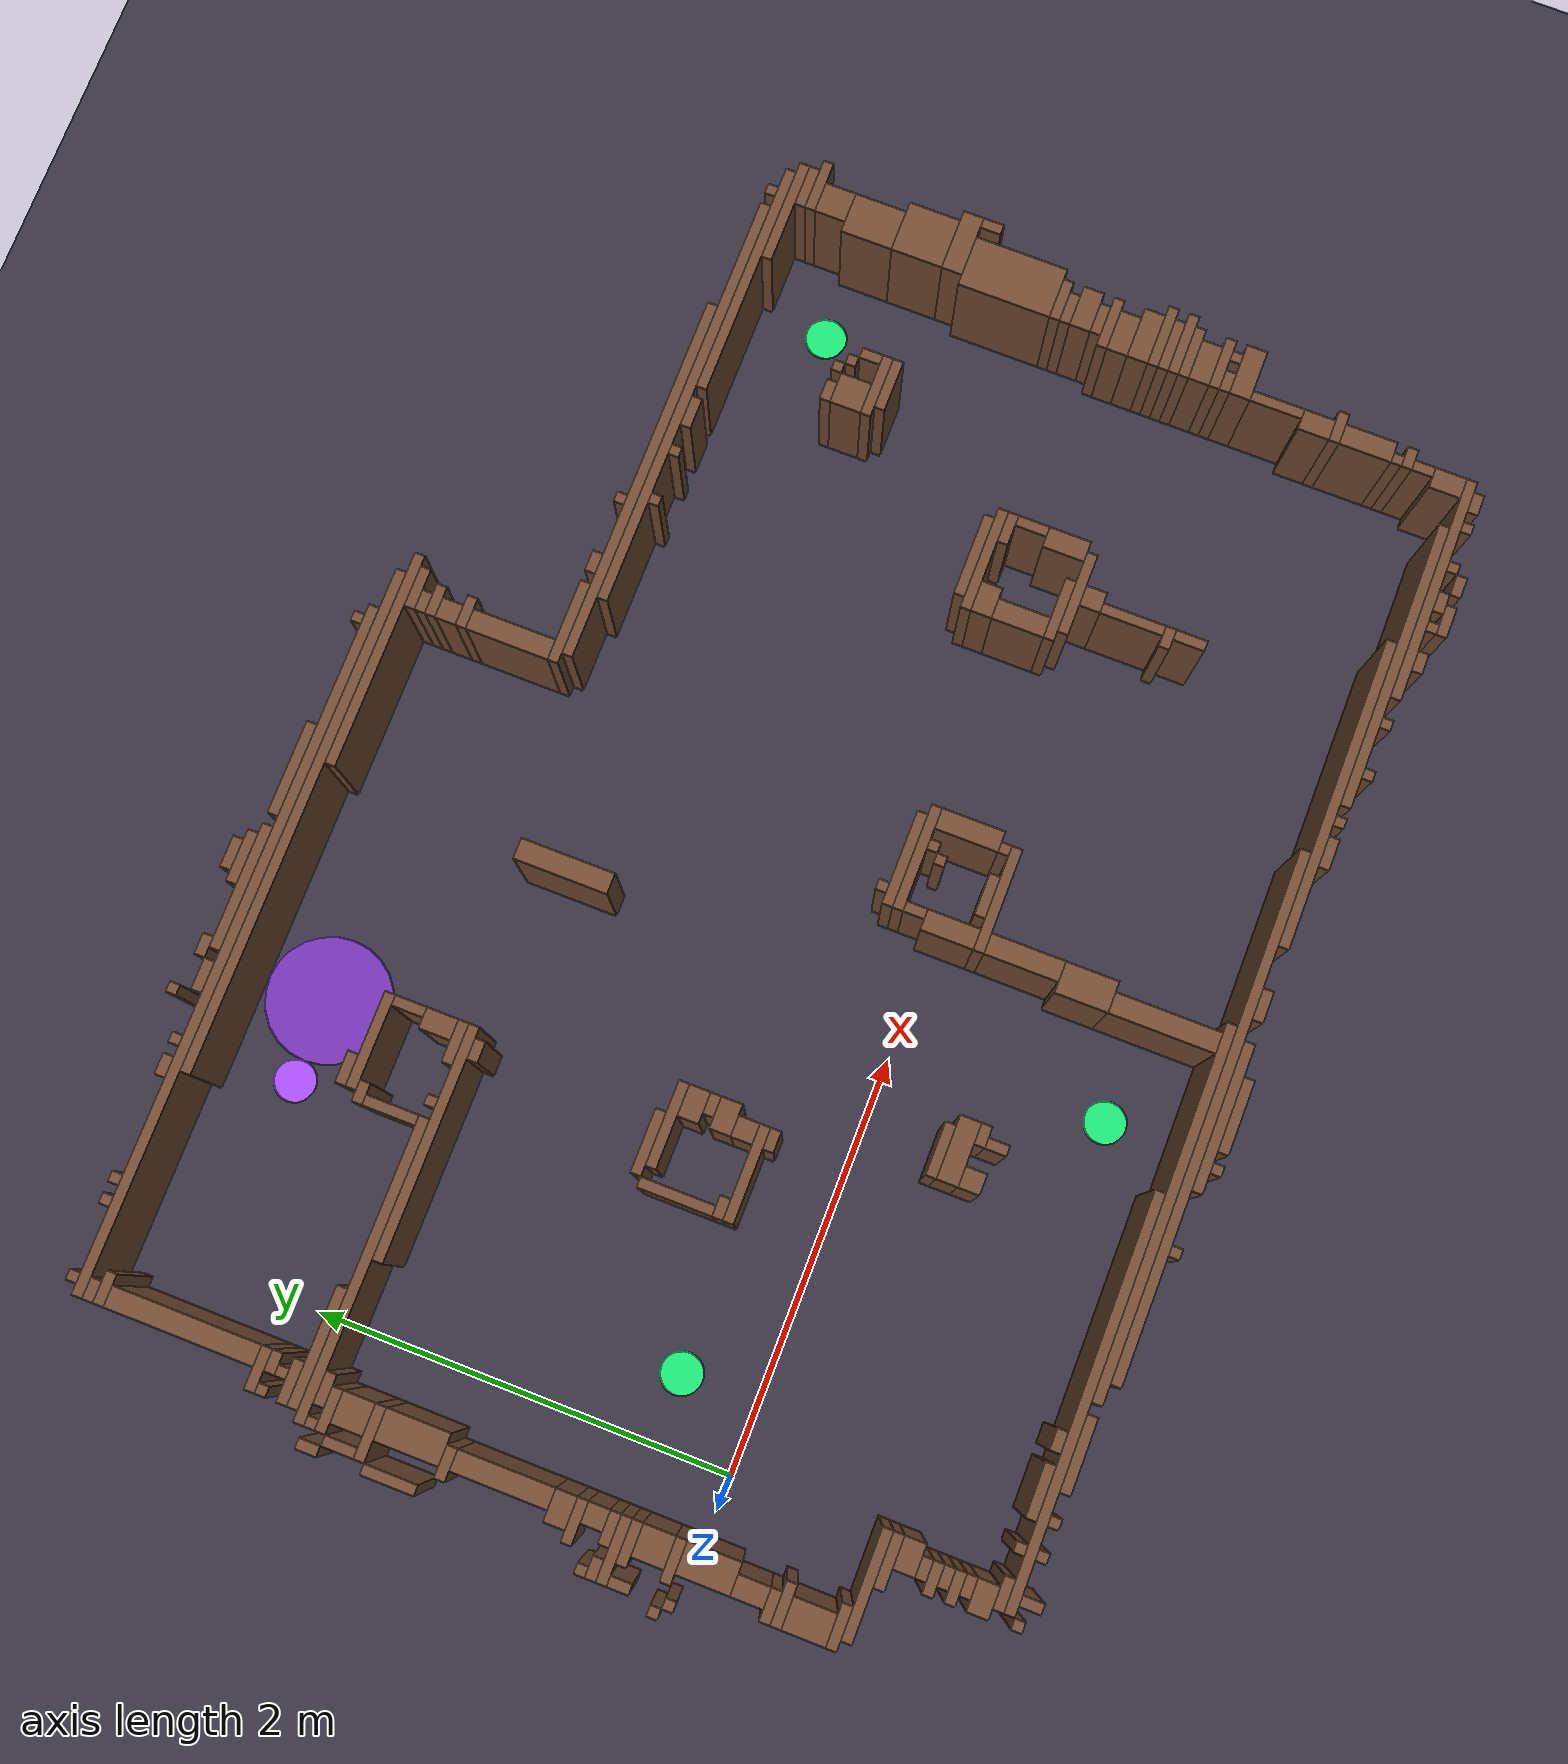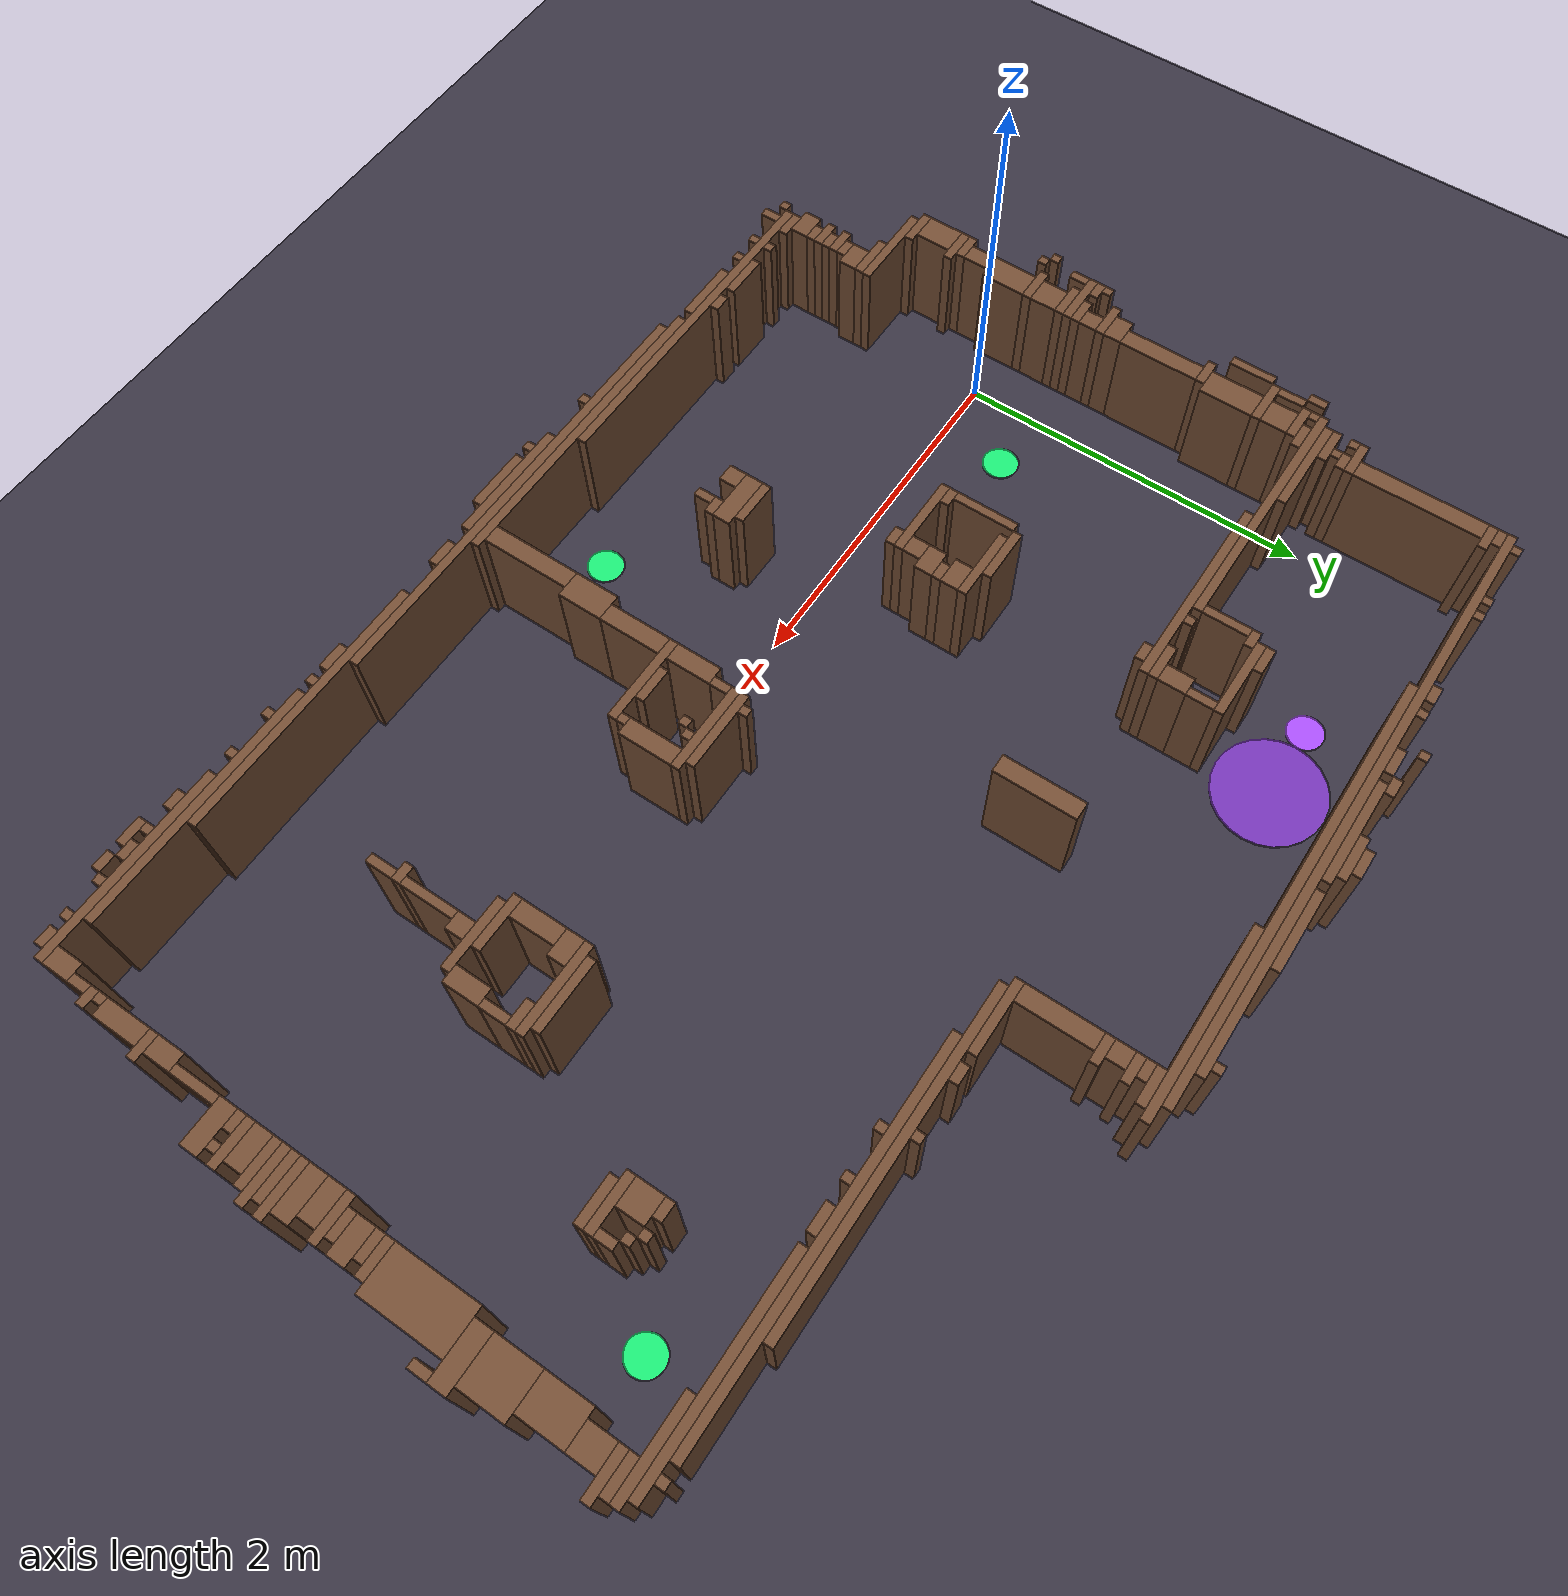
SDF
<?xml version="1.0"?>
<!-- map_to_world.py로 생성: holloween.yaml + level1.yaml. 직접 고치지 말고 맵·레벨을 바꾼 뒤 다시 생성할 것 -->
<sdf version='1.8'>
  <world name='holloween'>
    <physics name='1ms' type='ignored'>
      <max_step_size>0.006</max_step_size>
      <real_time_factor>1</real_time_factor>
      <real_time_update_rate>167</real_time_update_rate>
    </physics>
    <plugin name="gz::sim::systems::Physics" filename="gz-sim-physics-system" />
    <plugin name="gz::sim::systems::UserCommands" filename="gz-sim-user-commands-system" />
    <plugin name="gz::sim::systems::SceneBroadcaster" filename="gz-sim-scene-broadcaster-system" />
    <plugin name="gz::sim::systems::Contact" filename="gz-sim-contact-system" />
    <!-- 센서(카메라·라이다) 시스템은 월드에서 한 번만 불러온다. 로봇마다 불러오면 두 번째 로봇에서 Gazebo가 죽는다
         (Ogre ItemIdentityException). 그래서 런치가 로봇 모델에서 이 플러그인을 뺀 사본을 쓴다 -->
    <plugin name="gz::sim::systems::Sensors" filename="gz-sim-sensors-system">
      <render_engine>ogre2</render_engine>
    </plugin>
    <light name='sun' type='directional'>
      <cast_shadows>1</cast_shadows>
      <pose>0 0 10 0 0 0</pose>
      <diffuse>0.8 0.8 0.8 1</diffuse>
      <specular>0.2 0.2 0.2 1</specular>
      <direction>-0.5 0.1 -0.9</direction>
    </light>
    <gravity>0 0 -9.8</gravity>
    <scene>
      <ambient>0.45 0.42 0.5 1</ambient>
      <background>0.08 0.06 0.12 1</background>
      <shadows>1</shadows>
    </scene>
    <model name='ground_plane'>
      <static>true</static>
      <link name='link'>
        <collision name='collision'><geometry><plane><normal>0 0 1</normal><size>100 100</size></plane></geometry></collision>
        <visual name='visual'>
          <geometry><plane><normal>0 0 1</normal><size>100 100</size></plane></geometry>
          <material><ambient>0.22 0.2 0.26 1</ambient><diffuse>0.22 0.2 0.26 1</diffuse></material>
        </visual>
      </link>
    </model>
    <model name='wall_0'><static>true</static><pose>1.103 3.049 0.300 0 0 0</pose><link name='l'><collision name='c'><geometry><box><size>0.050 0.050 0.600</size></box></geometry></collision><visual name='v'><geometry><box><size>0.050 0.050 0.600</size></box></geometry><material><ambient>0.45 0.3 0.2 1</ambient><diffuse>0.45 0.3 0.2 1</diffuse></material></visual></link></model>
    <model name='wall_1'><static>true</static><pose>1.753 3.049 0.300 0 0 0</pose><link name='l'><collision name='c'><geometry><box><size>0.150 0.050 0.600</size></box></geometry></collision><visual name='v'><geometry><box><size>0.150 0.050 0.600</size></box></geometry><material><ambient>0.45 0.3 0.2 1</ambient><diffuse>0.45 0.3 0.2 1</diffuse></material></visual></link></model>
    <model name='wall_2'><static>true</static><pose>1.328 2.999 0.300 0 0 0</pose><link name='l'><collision name='c'><geometry><box><size>0.100 0.050 0.600</size></box></geometry></collision><visual name='v'><geometry><box><size>0.100 0.050 0.600</size></box></geometry><material><ambient>0.45 0.3 0.2 1</ambient><diffuse>0.45 0.3 0.2 1</diffuse></material></visual></link></model>
    <model name='wall_3'><static>true</static><pose>1.753 2.999 0.300 0 0 0</pose><link name='l'><collision name='c'><geometry><box><size>0.250 0.050 0.600</size></box></geometry></collision><visual name='v'><geometry><box><size>0.250 0.050 0.600</size></box></geometry><material><ambient>0.45 0.3 0.2 1</ambient><diffuse>0.45 0.3 0.2 1</diffuse></material></visual></link></model>
    <model name='wall_4'><static>true</static><pose>-0.197 2.949 0.300 0 0 0</pose><link name='l'><collision name='c'><geometry><box><size>0.050 0.050 0.600</size></box></geometry></collision><visual name='v'><geometry><box><size>0.050 0.050 0.600</size></box></geometry><material><ambient>0.45 0.3 0.2 1</ambient><diffuse>0.45 0.3 0.2 1</diffuse></material></visual></link></model>
    <model name='wall_5'><static>true</static><pose>2.953 2.949 0.300 0 0 0</pose><link name='l'><collision name='c'><geometry><box><size>0.050 0.050 0.600</size></box></geometry></collision><visual name='v'><geometry><box><size>0.050 0.050 0.600</size></box></geometry><material><ambient>0.45 0.3 0.2 1</ambient><diffuse>0.45 0.3 0.2 1</diffuse></material></visual></link></model>
    <model name='wall_6'><static>true</static><pose>1.628 2.949 0.300 0 0 0</pose><link name='l'><collision name='c'><geometry><box><size>0.600 0.050 0.600</size></box></geometry></collision><visual name='v'><geometry><box><size>0.600 0.050 0.600</size></box></geometry><material><ambient>0.45 0.3 0.2 1</ambient><diffuse>0.45 0.3 0.2 1</diffuse></material></visual></link></model>
    <model name='wall_7'><static>true</static><pose>1.203 2.949 0.300 0 0 0</pose><link name='l'><collision name='c'><geometry><box><size>0.150 0.050 0.600</size></box></geometry></collision><visual name='v'><geometry><box><size>0.150 0.050 0.600</size></box></geometry><material><ambient>0.45 0.3 0.2 1</ambient><diffuse>0.45 0.3 0.2 1</diffuse></material></visual></link></model>
    <model name='wall_8'><static>true</static><pose>2.203 2.949 0.300 0 0 0</pose><link name='l'><collision name='c'><geometry><box><size>0.450 0.050 0.600</size></box></geometry></collision><visual name='v'><geometry><box><size>0.450 0.050 0.600</size></box></geometry><material><ambient>0.45 0.3 0.2 1</ambient><diffuse>0.45 0.3 0.2 1</diffuse></material></visual></link></model>
    <model name='wall_9'><static>true</static><pose>0.253 2.949 0.300 0 0 0</pose><link name='l'><collision name='c'><geometry><box><size>0.050 0.050 0.600</size></box></geometry></collision><visual name='v'><geometry><box><size>0.050 0.050 0.600</size></box></geometry><material><ambient>0.45 0.3 0.2 1</ambient><diffuse>0.45 0.3 0.2 1</diffuse></material></visual></link></model>
    <model name='wall_10'><static>true</static><pose>0.903 2.949 0.300 0 0 0</pose><link name='l'><collision name='c'><geometry><box><size>0.050 0.050 0.600</size></box></geometry></collision><visual name='v'><geometry><box><size>0.050 0.050 0.600</size></box></geometry><material><ambient>0.45 0.3 0.2 1</ambient><diffuse>0.45 0.3 0.2 1</diffuse></material></visual></link></model>
    <model name='wall_11'><static>true</static><pose>0.778 2.949 0.300 0 0 0</pose><link name='l'><collision name='c'><geometry><box><size>0.100 0.050 0.600</size></box></geometry></collision><visual name='v'><geometry><box><size>0.100 0.050 0.600</size></box></geometry><material><ambient>0.45 0.3 0.2 1</ambient><diffuse>0.45 0.3 0.2 1</diffuse></material></visual></link></model>
    <model name='wall_12'><static>true</static><pose>0.153 2.949 0.300 0 0 0</pose><link name='l'><collision name='c'><geometry><box><size>0.050 0.050 0.600</size></box></geometry></collision><visual name='v'><geometry><box><size>0.050 0.050 0.600</size></box></geometry><material><ambient>0.45 0.3 0.2 1</ambient><diffuse>0.45 0.3 0.2 1</diffuse></material></visual></link></model>
    <model name='wall_13'><static>true</static><pose>1.378 2.899 0.300 0 0 0</pose><link name='l'><collision name='c'><geometry><box><size>3.300 0.050 0.600</size></box></geometry></collision><visual name='v'><geometry><box><size>3.300 0.050 0.600</size></box></geometry><material><ambient>0.45 0.3 0.2 1</ambient><diffuse>0.45 0.3 0.2 1</diffuse></material></visual></link></model>
    <model name='wall_14'><static>true</static><pose>2.003 2.849 0.300 0 0 0</pose><link name='l'><collision name='c'><geometry><box><size>2.450 0.050 0.600</size></box></geometry></collision><visual name='v'><geometry><box><size>2.450 0.050 0.600</size></box></geometry><material><ambient>0.45 0.3 0.2 1</ambient><diffuse>0.45 0.3 0.2 1</diffuse></material></visual></link></model>
    <model name='wall_15'><static>true</static><pose>-0.222 2.849 0.300 0 0 0</pose><link name='l'><collision name='c'><geometry><box><size>0.100 0.050 0.600</size></box></geometry></collision><visual name='v'><geometry><box><size>0.100 0.050 0.600</size></box></geometry><material><ambient>0.45 0.3 0.2 1</ambient><diffuse>0.45 0.3 0.2 1</diffuse></material></visual></link></model>
    <model name='wall_16'><static>true</static><pose>-0.197 2.799 0.300 0 0 0</pose><link name='l'><collision name='c'><geometry><box><size>0.150 0.050 0.600</size></box></geometry></collision><visual name='v'><geometry><box><size>0.150 0.050 0.600</size></box></geometry><material><ambient>0.45 0.3 0.2 1</ambient><diffuse>0.45 0.3 0.2 1</diffuse></material></visual></link></model>
    <model name='wall_17'><static>true</static><pose>2.803 2.799 0.300 0 0 0</pose><link name='l'><collision name='c'><geometry><box><size>1.050 0.050 0.600</size></box></geometry></collision><visual name='v'><geometry><box><size>1.050 0.050 0.600</size></box></geometry><material><ambient>0.45 0.3 0.2 1</ambient><diffuse>0.45 0.3 0.2 1</diffuse></material></visual></link></model>
    <model name='wall_18'><static>true</static><pose>3.178 2.749 0.300 0 0 0</pose><link name='l'><collision name='c'><geometry><box><size>0.200 0.050 0.600</size></box></geometry></collision><visual name='v'><geometry><box><size>0.200 0.050 0.600</size></box></geometry><material><ambient>0.45 0.3 0.2 1</ambient><diffuse>0.45 0.3 0.2 1</diffuse></material></visual></link></model>
    <model name='wall_19'><static>true</static><pose>3.128 2.699 0.300 0 0 0</pose><link name='l'><collision name='c'><geometry><box><size>0.100 0.050 0.600</size></box></geometry></collision><visual name='v'><geometry><box><size>0.100 0.050 0.600</size></box></geometry><material><ambient>0.45 0.3 0.2 1</ambient><diffuse>0.45 0.3 0.2 1</diffuse></material></visual></link></model>
    <model name='wall_20'><static>true</static><pose>3.153 2.649 0.300 0 0 0</pose><link name='l'><collision name='c'><geometry><box><size>0.150 0.050 0.600</size></box></geometry></collision><visual name='v'><geometry><box><size>0.150 0.050 0.600</size></box></geometry><material><ambient>0.45 0.3 0.2 1</ambient><diffuse>0.45 0.3 0.2 1</diffuse></material></visual></link></model>
    <model name='wall_21'><static>true</static><pose>3.128 2.574 0.300 0 0 0</pose><link name='l'><collision name='c'><geometry><box><size>0.100 0.100 0.600</size></box></geometry></collision><visual name='v'><geometry><box><size>0.100 0.100 0.600</size></box></geometry><material><ambient>0.45 0.3 0.2 1</ambient><diffuse>0.45 0.3 0.2 1</diffuse></material></visual></link></model>
    <model name='wall_22'><static>true</static><pose>3.153 2.499 0.300 0 0 0</pose><link name='l'><collision name='c'><geometry><box><size>0.150 0.050 0.600</size></box></geometry></collision><visual name='v'><geometry><box><size>0.150 0.050 0.600</size></box></geometry><material><ambient>0.45 0.3 0.2 1</ambient><diffuse>0.45 0.3 0.2 1</diffuse></material></visual></link></model>
    <model name='wall_23'><static>true</static><pose>1.053 2.199 0.300 0 0 0</pose><link name='l'><collision name='c'><geometry><box><size>0.150 0.050 0.600</size></box></geometry></collision><visual name='v'><geometry><box><size>0.150 0.050 0.600</size></box></geometry><material><ambient>0.45 0.3 0.2 1</ambient><diffuse>0.45 0.3 0.2 1</diffuse></material></visual></link></model>
    <model name='wall_24'><static>true</static><pose>1.203 2.149 0.300 0 0 0</pose><link name='l'><collision name='c'><geometry><box><size>0.450 0.050 0.600</size></box></geometry></collision><visual name='v'><geometry><box><size>0.450 0.050 0.600</size></box></geometry><material><ambient>0.45 0.3 0.2 1</ambient><diffuse>0.45 0.3 0.2 1</diffuse></material></visual></link></model>
    <model name='wall_25'><static>true</static><pose>-0.222 2.424 0.300 0 0 0</pose><link name='l'><collision name='c'><geometry><box><size>0.100 0.700 0.600</size></box></geometry></collision><visual name='v'><geometry><box><size>0.100 0.700 0.600</size></box></geometry><material><ambient>0.45 0.3 0.2 1</ambient><diffuse>0.45 0.3 0.2 1</diffuse></material></visual></link></model>
    <model name='wall_26'><static>true</static><pose>3.128 2.274 0.300 0 0 0</pose><link name='l'><collision name='c'><geometry><box><size>0.100 0.400 0.600</size></box></geometry></collision><visual name='v'><geometry><box><size>0.100 0.400 0.600</size></box></geometry><material><ambient>0.45 0.3 0.2 1</ambient><diffuse>0.45 0.3 0.2 1</diffuse></material></visual></link></model>
    <model name='wall_27'><static>true</static><pose>0.978 2.099 0.300 0 0 0</pose><link name='l'><collision name='c'><geometry><box><size>0.100 0.050 0.600</size></box></geometry></collision><visual name='v'><geometry><box><size>0.100 0.050 0.600</size></box></geometry><material><ambient>0.45 0.3 0.2 1</ambient><diffuse>0.45 0.3 0.2 1</diffuse></material></visual></link></model>
    <model name='wall_28'><static>true</static><pose>3.278 2.049 0.300 0 0 0</pose><link name='l'><collision name='c'><geometry><box><size>0.400 0.050 0.600</size></box></geometry></collision><visual name='v'><geometry><box><size>0.400 0.050 0.600</size></box></geometry><material><ambient>0.45 0.3 0.2 1</ambient><diffuse>0.45 0.3 0.2 1</diffuse></material></visual></link></model>
    <model name='wall_29'><static>true</static><pose>-0.272 2.049 0.300 0 0 0</pose><link name='l'><collision name='c'><geometry><box><size>0.200 0.050 0.600</size></box></geometry></collision><visual name='v'><geometry><box><size>0.200 0.050 0.600</size></box></geometry><material><ambient>0.45 0.3 0.2 1</ambient><diffuse>0.45 0.3 0.2 1</diffuse></material></visual></link></model>
    <model name='wall_30'><static>true</static><pose>3.578 2.049 0.300 0 0 0</pose><link name='l'><collision name='c'><geometry><box><size>0.100 0.050 0.600</size></box></geometry></collision><visual name='v'><geometry><box><size>0.100 0.050 0.600</size></box></geometry><material><ambient>0.45 0.3 0.2 1</ambient><diffuse>0.45 0.3 0.2 1</diffuse></material></visual></link></model>
    <model name='wall_31'><static>true</static><pose>3.903 2.049 0.300 0 0 0</pose><link name='l'><collision name='c'><geometry><box><size>0.050 0.050 0.600</size></box></geometry></collision><visual name='v'><geometry><box><size>0.050 0.050 0.600</size></box></geometry><material><ambient>0.45 0.3 0.2 1</ambient><diffuse>0.45 0.3 0.2 1</diffuse></material></visual></link></model>
    <model name='wall_32'><static>true</static><pose>1.403 2.049 0.300 0 0 0</pose><link name='l'><collision name='c'><geometry><box><size>0.050 0.150 0.600</size></box></geometry></collision><visual name='v'><geometry><box><size>0.050 0.150 0.600</size></box></geometry><material><ambient>0.45 0.3 0.2 1</ambient><diffuse>0.45 0.3 0.2 1</diffuse></material></visual></link></model>
    <model name='wall_33'><static>true</static><pose>-0.222 1.999 0.300 0 0 0</pose><link name='l'><collision name='c'><geometry><box><size>0.100 0.050 0.600</size></box></geometry></collision><visual name='v'><geometry><box><size>0.100 0.050 0.600</size></box></geometry><material><ambient>0.45 0.3 0.2 1</ambient><diffuse>0.45 0.3 0.2 1</diffuse></material></visual></link></model>
    <model name='wall_34'><static>true</static><pose>-0.347 1.999 0.300 0 0 0</pose><link name='l'><collision name='c'><geometry><box><size>0.050 0.050 0.600</size></box></geometry></collision><visual name='v'><geometry><box><size>0.050 0.050 0.600</size></box></geometry><material><ambient>0.45 0.3 0.2 1</ambient><diffuse>0.45 0.3 0.2 1</diffuse></material></visual></link></model>
    <model name='wall_35'><static>true</static><pose>4.028 1.999 0.300 0 0 0</pose><link name='l'><collision name='c'><geometry><box><size>1.800 0.050 0.600</size></box></geometry></collision><visual name='v'><geometry><box><size>1.800 0.050 0.600</size></box></geometry><material><ambient>0.45 0.3 0.2 1</ambient><diffuse>0.45 0.3 0.2 1</diffuse></material></visual></link></model>
    <model name='wall_36'><static>true</static><pose>-0.247 1.949 0.300 0 0 0</pose><link name='l'><collision name='c'><geometry><box><size>0.050 0.050 0.600</size></box></geometry></collision><visual name='v'><geometry><box><size>0.050 0.050 0.600</size></box></geometry><material><ambient>0.45 0.3 0.2 1</ambient><diffuse>0.45 0.3 0.2 1</diffuse></material></visual></link></model>
    <model name='wall_37'><static>true</static><pose>5.553 1.949 0.300 0 0 0</pose><link name='l'><collision name='c'><geometry><box><size>0.050 0.050 0.600</size></box></geometry></collision><visual name='v'><geometry><box><size>0.050 0.050 0.600</size></box></geometry><material><ambient>0.45 0.3 0.2 1</ambient><diffuse>0.45 0.3 0.2 1</diffuse></material></visual></link></model>
    <model name='wall_38'><static>true</static><pose>4.453 1.949 0.300 0 0 0</pose><link name='l'><collision name='c'><geometry><box><size>2.050 0.050 0.600</size></box></geometry></collision><visual name='v'><geometry><box><size>2.050 0.050 0.600</size></box></geometry><material><ambient>0.45 0.3 0.2 1</ambient><diffuse>0.45 0.3 0.2 1</diffuse></material></visual></link></model>
    <model name='wall_39'><static>true</static><pose>4.403 1.899 0.300 0 0 0</pose><link name='l'><collision name='c'><geometry><box><size>0.150 0.050 0.600</size></box></geometry></collision><visual name='v'><geometry><box><size>0.150 0.050 0.600</size></box></geometry><material><ambient>0.45 0.3 0.2 1</ambient><diffuse>0.45 0.3 0.2 1</diffuse></material></visual></link></model>
    <model name='wall_40'><static>true</static><pose>3.953 1.899 0.300 0 0 0</pose><link name='l'><collision name='c'><geometry><box><size>0.050 0.050 0.600</size></box></geometry></collision><visual name='v'><geometry><box><size>0.050 0.050 0.600</size></box></geometry><material><ambient>0.45 0.3 0.2 1</ambient><diffuse>0.45 0.3 0.2 1</diffuse></material></visual></link></model>
    <model name='wall_41'><static>true</static><pose>-0.272 1.899 0.300 0 0 0</pose><link name='l'><collision name='c'><geometry><box><size>0.200 0.050 0.600</size></box></geometry></collision><visual name='v'><geometry><box><size>0.200 0.050 0.600</size></box></geometry><material><ambient>0.45 0.3 0.2 1</ambient><diffuse>0.45 0.3 0.2 1</diffuse></material></visual></link></model>
    <model name='wall_42'><static>true</static><pose>5.103 1.899 0.300 0 0 0</pose><link name='l'><collision name='c'><geometry><box><size>1.150 0.050 0.600</size></box></geometry></collision><visual name='v'><geometry><box><size>1.150 0.050 0.600</size></box></geometry><material><ambient>0.45 0.3 0.2 1</ambient><diffuse>0.45 0.3 0.2 1</diffuse></material></visual></link></model>
    <model name='wall_43'><static>true</static><pose>4.203 1.899 0.300 0 0 0</pose><link name='l'><collision name='c'><geometry><box><size>0.050 0.050 0.600</size></box></geometry></collision><visual name='v'><geometry><box><size>0.050 0.050 0.600</size></box></geometry><material><ambient>0.45 0.3 0.2 1</ambient><diffuse>0.45 0.3 0.2 1</diffuse></material></visual></link></model>
    <model name='wall_44'><static>true</static><pose>0.953 1.949 0.300 0 0 0</pose><link name='l'><collision name='c'><geometry><box><size>0.050 0.250 0.600</size></box></geometry></collision><visual name='v'><geometry><box><size>0.050 0.250 0.600</size></box></geometry><material><ambient>0.45 0.3 0.2 1</ambient><diffuse>0.45 0.3 0.2 1</diffuse></material></visual></link></model>
    <model name='wall_45'><static>true</static><pose>1.378 1.899 0.300 0 0 0</pose><link name='l'><collision name='c'><geometry><box><size>0.100 0.150 0.600</size></box></geometry></collision><visual name='v'><geometry><box><size>0.100 0.150 0.600</size></box></geometry><material><ambient>0.45 0.3 0.2 1</ambient><diffuse>0.45 0.3 0.2 1</diffuse></material></visual></link></model>
    <model name='wall_46'><static>true</static><pose>-0.097 1.849 0.300 0 0 0</pose><link name='l'><collision name='c'><geometry><box><size>0.550 0.050 0.600</size></box></geometry></collision><visual name='v'><geometry><box><size>0.550 0.050 0.600</size></box></geometry><material><ambient>0.45 0.3 0.2 1</ambient><diffuse>0.45 0.3 0.2 1</diffuse></material></visual></link></model>
    <model name='wall_47'><static>true</static><pose>5.478 1.849 0.300 0 0 0</pose><link name='l'><collision name='c'><geometry><box><size>0.500 0.050 0.600</size></box></geometry></collision><visual name='v'><geometry><box><size>0.500 0.050 0.600</size></box></geometry><material><ambient>0.45 0.3 0.2 1</ambient><diffuse>0.45 0.3 0.2 1</diffuse></material></visual></link></model>
    <model name='wall_48'><static>true</static><pose>1.328 1.799 0.300 0 0 0</pose><link name='l'><collision name='c'><geometry><box><size>0.200 0.050 0.600</size></box></geometry></collision><visual name='v'><geometry><box><size>0.200 0.050 0.600</size></box></geometry><material><ambient>0.45 0.3 0.2 1</ambient><diffuse>0.45 0.3 0.2 1</diffuse></material></visual></link></model>
    <model name='wall_49'><static>true</static><pose>0.278 1.799 0.300 0 0 0</pose><link name='l'><collision name='c'><geometry><box><size>1.400 0.050 0.600</size></box></geometry></collision><visual name='v'><geometry><box><size>1.400 0.050 0.600</size></box></geometry><material><ambient>0.45 0.3 0.2 1</ambient><diffuse>0.45 0.3 0.2 1</diffuse></material></visual></link></model>
    <model name='wall_50'><static>true</static><pose>1.053 1.799 0.300 0 0 0</pose><link name='l'><collision name='c'><geometry><box><size>0.050 0.050 0.600</size></box></geometry></collision><visual name='v'><geometry><box><size>0.050 0.050 0.600</size></box></geometry><material><ambient>0.45 0.3 0.2 1</ambient><diffuse>0.45 0.3 0.2 1</diffuse></material></visual></link></model>
    <model name='wall_51'><static>true</static><pose>5.628 1.799 0.300 0 0 0</pose><link name='l'><collision name='c'><geometry><box><size>0.200 0.050 0.600</size></box></geometry></collision><visual name='v'><geometry><box><size>0.200 0.050 0.600</size></box></geometry><material><ambient>0.45 0.3 0.2 1</ambient><diffuse>0.45 0.3 0.2 1</diffuse></material></visual></link></model>
    <model name='wall_52'><static>true</static><pose>-0.247 1.749 0.300 0 0 0</pose><link name='l'><collision name='c'><geometry><box><size>0.150 0.050 0.600</size></box></geometry></collision><visual name='v'><geometry><box><size>0.150 0.050 0.600</size></box></geometry><material><ambient>0.45 0.3 0.2 1</ambient><diffuse>0.45 0.3 0.2 1</diffuse></material></visual></link></model>
    <model name='wall_53'><static>true</static><pose>5.653 1.749 0.300 0 0 0</pose><link name='l'><collision name='c'><geometry><box><size>0.250 0.050 0.600</size></box></geometry></collision><visual name='v'><geometry><box><size>0.250 0.050 0.600</size></box></geometry><material><ambient>0.45 0.3 0.2 1</ambient><diffuse>0.45 0.3 0.2 1</diffuse></material></visual></link></model>
    <model name='wall_54'><static>true</static><pose>0.878 1.749 0.300 0 0 0</pose><link name='l'><collision name='c'><geometry><box><size>1.100 0.050 0.600</size></box></geometry></collision><visual name='v'><geometry><box><size>1.100 0.050 0.600</size></box></geometry><material><ambient>0.45 0.3 0.2 1</ambient><diffuse>0.45 0.3 0.2 1</diffuse></material></visual></link></model>
    <model name='wall_55'><static>true</static><pose>-0.397 1.749 0.300 0 0 0</pose><link name='l'><collision name='c'><geometry><box><size>0.050 0.050 0.600</size></box></geometry></collision><visual name='v'><geometry><box><size>0.050 0.050 0.600</size></box></geometry><material><ambient>0.45 0.3 0.2 1</ambient><diffuse>0.45 0.3 0.2 1</diffuse></material></visual></link></model>
    <model name='wall_56'><static>true</static><pose>-0.497 1.724 0.300 0 0 0</pose><link name='l'><collision name='c'><geometry><box><size>0.050 0.100 0.600</size></box></geometry></collision><visual name='v'><geometry><box><size>0.050 0.100 0.600</size></box></geometry><material><ambient>0.45 0.3 0.2 1</ambient><diffuse>0.45 0.3 0.2 1</diffuse></material></visual></link></model>
    <model name='wall_57'><static>true</static><pose>-0.322 1.699 0.300 0 0 0</pose><link name='l'><collision name='c'><geometry><box><size>0.200 0.050 0.600</size></box></geometry></collision><visual name='v'><geometry><box><size>0.200 0.050 0.600</size></box></geometry><material><ambient>0.45 0.3 0.2 1</ambient><diffuse>0.45 0.3 0.2 1</diffuse></material></visual></link></model>
    <model name='wall_58'><static>true</static><pose>1.328 1.699 0.300 0 0 0</pose><link name='l'><collision name='c'><geometry><box><size>0.100 0.050 0.600</size></box></geometry></collision><visual name='v'><geometry><box><size>0.100 0.050 0.600</size></box></geometry><material><ambient>0.45 0.3 0.2 1</ambient><diffuse>0.45 0.3 0.2 1</diffuse></material></visual></link></model>
    <model name='wall_59'><static>true</static><pose>5.603 1.649 0.300 0 0 0</pose><link name='l'><collision name='c'><geometry><box><size>0.150 0.150 0.600</size></box></geometry></collision><visual name='v'><geometry><box><size>0.150 0.150 0.600</size></box></geometry><material><ambient>0.45 0.3 0.2 1</ambient><diffuse>0.45 0.3 0.2 1</diffuse></material></visual></link></model>
    <model name='wall_60'><static>true</static><pose>-0.447 1.599 0.300 0 0 0</pose><link name='l'><collision name='c'><geometry><box><size>0.050 0.150 0.600</size></box></geometry></collision><visual name='v'><geometry><box><size>0.050 0.150 0.600</size></box></geometry><material><ambient>0.45 0.3 0.2 1</ambient><diffuse>0.45 0.3 0.2 1</diffuse></material></visual></link></model>
    <model name='wall_61'><static>true</static><pose>-0.297 1.599 0.300 0 0 0</pose><link name='l'><collision name='c'><geometry><box><size>0.150 0.150 0.600</size></box></geometry></collision><visual name='v'><geometry><box><size>0.150 0.150 0.600</size></box></geometry><material><ambient>0.45 0.3 0.2 1</ambient><diffuse>0.45 0.3 0.2 1</diffuse></material></visual></link></model>
    <model name='wall_62'><static>true</static><pose>-0.347 1.499 0.300 0 0 0</pose><link name='l'><collision name='c'><geometry><box><size>0.250 0.050 0.600</size></box></geometry></collision><visual name='v'><geometry><box><size>0.250 0.050 0.600</size></box></geometry><material><ambient>0.45 0.3 0.2 1</ambient><diffuse>0.45 0.3 0.2 1</diffuse></material></visual></link></model>
    <model name='wall_63'><static>true</static><pose>2.228 1.649 0.300 0 0 0</pose><link name='l'><collision name='c'><geometry><box><size>0.100 0.450 0.600</size></box></geometry></collision><visual name='v'><geometry><box><size>0.100 0.450 0.600</size></box></geometry><material><ambient>0.45 0.3 0.2 1</ambient><diffuse>0.45 0.3 0.2 1</diffuse></material></visual></link></model>
    <model name='wall_64'><static>true</static><pose>5.578 1.449 0.300 0 0 0</pose><link name='l'><collision name='c'><geometry><box><size>0.200 0.250 0.600</size></box></geometry></collision><visual name='v'><geometry><box><size>0.200 0.250 0.600</size></box></geometry><material><ambient>0.45 0.3 0.2 1</ambient><diffuse>0.45 0.3 0.2 1</diffuse></material></visual></link></model>
    <model name='wall_65'><static>true</static><pose>4.853 1.349 0.300 0 0 0</pose><link name='l'><collision name='c'><geometry><box><size>0.050 0.050 0.600</size></box></geometry></collision><visual name='v'><geometry><box><size>0.050 0.050 0.600</size></box></geometry><material><ambient>0.45 0.3 0.2 1</ambient><diffuse>0.45 0.3 0.2 1</diffuse></material></visual></link></model>
    <model name='wall_66'><static>true</static><pose>4.728 1.349 0.300 0 0 0</pose><link name='l'><collision name='c'><geometry><box><size>0.100 0.050 0.600</size></box></geometry></collision><visual name='v'><geometry><box><size>0.100 0.050 0.600</size></box></geometry><material><ambient>0.45 0.3 0.2 1</ambient><diffuse>0.45 0.3 0.2 1</diffuse></material></visual></link></model>
    <model name='wall_67'><static>true</static><pose>4.903 1.299 0.300 0 0 0</pose><link name='l'><collision name='c'><geometry><box><size>0.050 0.050 0.600</size></box></geometry></collision><visual name='v'><geometry><box><size>0.050 0.050 0.600</size></box></geometry><material><ambient>0.45 0.3 0.2 1</ambient><diffuse>0.45 0.3 0.2 1</diffuse></material></visual></link></model>
    <model name='wall_68'><static>true</static><pose>-0.497 1.349 0.300 0 0 0</pose><link name='l'><collision name='c'><geometry><box><size>0.050 0.250 0.600</size></box></geometry></collision><visual name='v'><geometry><box><size>0.050 0.250 0.600</size></box></geometry><material><ambient>0.45 0.3 0.2 1</ambient><diffuse>0.45 0.3 0.2 1</diffuse></material></visual></link></model>
    <model name='wall_69'><static>true</static><pose>-0.297 1.324 0.300 0 0 0</pose><link name='l'><collision name='c'><geometry><box><size>0.150 0.300 0.600</size></box></geometry></collision><visual name='v'><geometry><box><size>0.150 0.300 0.600</size></box></geometry><material><ambient>0.45 0.3 0.2 1</ambient><diffuse>0.45 0.3 0.2 1</diffuse></material></visual></link></model>
    <model name='wall_70'><static>true</static><pose>4.753 1.249 0.300 0 0 0</pose><link name='l'><collision name='c'><geometry><box><size>0.150 0.150 0.600</size></box></geometry></collision><visual name='v'><geometry><box><size>0.150 0.150 0.600</size></box></geometry><material><ambient>0.45 0.3 0.2 1</ambient><diffuse>0.45 0.3 0.2 1</diffuse></material></visual></link></model>
    <model name='wall_71'><static>true</static><pose>4.953 1.224 0.300 0 0 0</pose><link name='l'><collision name='c'><geometry><box><size>0.050 0.100 0.600</size></box></geometry></collision><visual name='v'><geometry><box><size>0.050 0.100 0.600</size></box></geometry><material><ambient>0.45 0.3 0.2 1</ambient><diffuse>0.45 0.3 0.2 1</diffuse></material></visual></link></model>
    <model name='wall_72'><static>true</static><pose>4.828 1.149 0.300 0 0 0</pose><link name='l'><collision name='c'><geometry><box><size>0.300 0.050 0.600</size></box></geometry></collision><visual name='v'><geometry><box><size>0.300 0.050 0.600</size></box></geometry><material><ambient>0.45 0.3 0.2 1</ambient><diffuse>0.45 0.3 0.2 1</diffuse></material></visual></link></model>
    <model name='wall_73'><static>true</static><pose>-0.347 1.149 0.300 0 0 0</pose><link name='l'><collision name='c'><geometry><box><size>0.150 0.050 0.600</size></box></geometry></collision><visual name='v'><geometry><box><size>0.150 0.050 0.600</size></box></geometry><material><ambient>0.45 0.3 0.2 1</ambient><diffuse>0.45 0.3 0.2 1</diffuse></material></visual></link></model>
    <model name='wall_74'><static>true</static><pose>5.603 1.199 0.300 0 0 0</pose><link name='l'><collision name='c'><geometry><box><size>0.250 0.250 0.600</size></box></geometry></collision><visual name='v'><geometry><box><size>0.250 0.250 0.600</size></box></geometry><material><ambient>0.45 0.3 0.2 1</ambient><diffuse>0.45 0.3 0.2 1</diffuse></material></visual></link></model>
    <model name='wall_75'><static>true</static><pose>4.853 1.099 0.300 0 0 0</pose><link name='l'><collision name='c'><geometry><box><size>0.250 0.050 0.600</size></box></geometry></collision><visual name='v'><geometry><box><size>0.250 0.050 0.600</size></box></geometry><material><ambient>0.45 0.3 0.2 1</ambient><diffuse>0.45 0.3 0.2 1</diffuse></material></visual></link></model>
    <model name='wall_76'><static>true</static><pose>5.628 1.024 0.300 0 0 0</pose><link name='l'><collision name='c'><geometry><box><size>0.300 0.100 0.600</size></box></geometry></collision><visual name='v'><geometry><box><size>0.300 0.100 0.600</size></box></geometry><material><ambient>0.45 0.3 0.2 1</ambient><diffuse>0.45 0.3 0.2 1</diffuse></material></visual></link></model>
    <model name='wall_77'><static>true</static><pose>5.753 0.924 0.300 0 0 0</pose><link name='l'><collision name='c'><geometry><box><size>0.050 0.100 0.600</size></box></geometry></collision><visual name='v'><geometry><box><size>0.050 0.100 0.600</size></box></geometry><material><ambient>0.45 0.3 0.2 1</ambient><diffuse>0.45 0.3 0.2 1</diffuse></material></visual></link></model>
    <model name='wall_78'><static>true</static><pose>1.228 0.849 0.300 0 0 0</pose><link name='l'><collision name='c'><geometry><box><size>0.300 0.050 0.600</size></box></geometry></collision><visual name='v'><geometry><box><size>0.300 0.050 0.600</size></box></geometry><material><ambient>0.45 0.3 0.2 1</ambient><diffuse>0.45 0.3 0.2 1</diffuse></material></visual></link></model>
    <model name='wall_79'><static>true</static><pose>1.328 0.799 0.300 0 0 0</pose><link name='l'><collision name='c'><geometry><box><size>0.400 0.050 0.600</size></box></geometry></collision><visual name='v'><geometry><box><size>0.400 0.050 0.600</size></box></geometry><material><ambient>0.45 0.3 0.2 1</ambient><diffuse>0.45 0.3 0.2 1</diffuse></material></visual></link></model>
    <model name='wall_80'><static>true</static><pose>-0.322 0.899 0.300 0 0 0</pose><link name='l'><collision name='c'><geometry><box><size>0.100 0.450 0.600</size></box></geometry></collision><visual name='v'><geometry><box><size>0.100 0.450 0.600</size></box></geometry><material><ambient>0.45 0.3 0.2 1</ambient><diffuse>0.45 0.3 0.2 1</diffuse></material></visual></link></model>
    <model name='wall_81'><static>true</static><pose>1.453 0.724 0.300 0 0 0</pose><link name='l'><collision name='c'><geometry><box><size>0.150 0.100 0.600</size></box></geometry></collision><visual name='v'><geometry><box><size>0.150 0.100 0.600</size></box></geometry><material><ambient>0.45 0.3 0.2 1</ambient><diffuse>0.45 0.3 0.2 1</diffuse></material></visual></link></model>
    <model name='wall_82'><static>true</static><pose>1.478 0.649 0.300 0 0 0</pose><link name='l'><collision name='c'><geometry><box><size>0.100 0.050 0.600</size></box></geometry></collision><visual name='v'><geometry><box><size>0.100 0.050 0.600</size></box></geometry><material><ambient>0.45 0.3 0.2 1</ambient><diffuse>0.45 0.3 0.2 1</diffuse></material></visual></link></model>
    <model name='wall_83'><static>true</static><pose>-0.347 0.624 0.300 0 0 0</pose><link name='l'><collision name='c'><geometry><box><size>0.150 0.100 0.600</size></box></geometry></collision><visual name='v'><geometry><box><size>0.150 0.100 0.600</size></box></geometry><material><ambient>0.45 0.3 0.2 1</ambient><diffuse>0.45 0.3 0.2 1</diffuse></material></visual></link></model>
    <model name='wall_84'><static>true</static><pose>5.553 0.749 0.300 0 0 0</pose><link name='l'><collision name='c'><geometry><box><size>0.250 0.450 0.600</size></box></geometry></collision><visual name='v'><geometry><box><size>0.250 0.450 0.600</size></box></geometry><material><ambient>0.45 0.3 0.2 1</ambient><diffuse>0.45 0.3 0.2 1</diffuse></material></visual></link></model>
    <model name='wall_85'><static>true</static><pose>1.453 0.574 0.300 0 0 0</pose><link name='l'><collision name='c'><geometry><box><size>0.150 0.100 0.600</size></box></geometry></collision><visual name='v'><geometry><box><size>0.150 0.100 0.600</size></box></geometry><material><ambient>0.45 0.3 0.2 1</ambient><diffuse>0.45 0.3 0.2 1</diffuse></material></visual></link></model>
    <model name='wall_86'><static>true</static><pose>-0.372 0.549 0.300 0 0 0</pose><link name='l'><collision name='c'><geometry><box><size>0.200 0.050 0.600</size></box></geometry></collision><visual name='v'><geometry><box><size>0.200 0.050 0.600</size></box></geometry><material><ambient>0.45 0.3 0.2 1</ambient><diffuse>0.45 0.3 0.2 1</diffuse></material></visual></link></model>
    <model name='wall_87'><static>true</static><pose>1.053 0.649 0.300 0 0 0</pose><link name='l'><collision name='c'><geometry><box><size>0.050 0.350 0.600</size></box></geometry></collision><visual name='v'><geometry><box><size>0.050 0.350 0.600</size></box></geometry><material><ambient>0.45 0.3 0.2 1</ambient><diffuse>0.45 0.3 0.2 1</diffuse></material></visual></link></model>
    <model name='wall_88'><static>true</static><pose>5.528 0.499 0.300 0 0 0</pose><link name='l'><collision name='c'><geometry><box><size>0.200 0.050 0.600</size></box></geometry></collision><visual name='v'><geometry><box><size>0.200 0.050 0.600</size></box></geometry><material><ambient>0.45 0.3 0.2 1</ambient><diffuse>0.45 0.3 0.2 1</diffuse></material></visual></link></model>
    <model name='wall_89'><static>true</static><pose>-0.322 0.474 0.300 0 0 0</pose><link name='l'><collision name='c'><geometry><box><size>0.100 0.100 0.600</size></box></geometry></collision><visual name='v'><geometry><box><size>0.100 0.100 0.600</size></box></geometry><material><ambient>0.45 0.3 0.2 1</ambient><diffuse>0.45 0.3 0.2 1</diffuse></material></visual></link></model>
    <model name='wall_90'><static>true</static><pose>1.428 0.474 0.300 0 0 0</pose><link name='l'><collision name='c'><geometry><box><size>0.100 0.100 0.600</size></box></geometry></collision><visual name='v'><geometry><box><size>0.100 0.100 0.600</size></box></geometry><material><ambient>0.45 0.3 0.2 1</ambient><diffuse>0.45 0.3 0.2 1</diffuse></material></visual></link></model>
    <model name='wall_91'><static>true</static><pose>1.078 0.449 0.300 0 0 0</pose><link name='l'><collision name='c'><geometry><box><size>0.100 0.050 0.600</size></box></geometry></collision><visual name='v'><geometry><box><size>0.100 0.050 0.600</size></box></geometry><material><ambient>0.45 0.3 0.2 1</ambient><diffuse>0.45 0.3 0.2 1</diffuse></material></visual></link></model>
    <model name='wall_92'><static>true</static><pose>-0.547 0.449 0.300 0 0 0</pose><link name='l'><collision name='c'><geometry><box><size>0.050 0.050 0.600</size></box></geometry></collision><visual name='v'><geometry><box><size>0.050 0.050 0.600</size></box></geometry><material><ambient>0.45 0.3 0.2 1</ambient><diffuse>0.45 0.3 0.2 1</diffuse></material></visual></link></model>
    <model name='wall_93'><static>true</static><pose>4.228 0.449 0.300 0 0 0</pose><link name='l'><collision name='c'><geometry><box><size>0.400 0.050 0.600</size></box></geometry></collision><visual name='v'><geometry><box><size>0.400 0.050 0.600</size></box></geometry><material><ambient>0.45 0.3 0.2 1</ambient><diffuse>0.45 0.3 0.2 1</diffuse></material></visual></link></model>
    <model name='wall_94'><static>true</static><pose>5.503 0.449 0.300 0 0 0</pose><link name='l'><collision name='c'><geometry><box><size>0.150 0.050 0.600</size></box></geometry></collision><visual name='v'><geometry><box><size>0.150 0.050 0.600</size></box></geometry><material><ambient>0.45 0.3 0.2 1</ambient><diffuse>0.45 0.3 0.2 1</diffuse></material></visual></link></model>
    <model name='wall_95'><static>true</static><pose>1.253 0.399 0.300 0 0 0</pose><link name='l'><collision name='c'><geometry><box><size>0.450 0.050 0.600</size></box></geometry></collision><visual name='v'><geometry><box><size>0.450 0.050 0.600</size></box></geometry><material><ambient>0.45 0.3 0.2 1</ambient><diffuse>0.45 0.3 0.2 1</diffuse></material></visual></link></model>
    <model name='wall_96'><static>true</static><pose>-0.522 0.399 0.300 0 0 0</pose><link name='l'><collision name='c'><geometry><box><size>0.100 0.050 0.600</size></box></geometry></collision><visual name='v'><geometry><box><size>0.100 0.050 0.600</size></box></geometry><material><ambient>0.45 0.3 0.2 1</ambient><diffuse>0.45 0.3 0.2 1</diffuse></material></visual></link></model>
    <model name='wall_97'><static>true</static><pose>-0.347 0.399 0.300 0 0 0</pose><link name='l'><collision name='c'><geometry><box><size>0.150 0.050 0.600</size></box></geometry></collision><visual name='v'><geometry><box><size>0.150 0.050 0.600</size></box></geometry><material><ambient>0.45 0.3 0.2 1</ambient><diffuse>0.45 0.3 0.2 1</diffuse></material></visual></link></model>
    <model name='wall_98'><static>true</static><pose>4.228 0.399 0.300 0 0 0</pose><link name='l'><collision name='c'><geometry><box><size>0.500 0.050 0.600</size></box></geometry></collision><visual name='v'><geometry><box><size>0.500 0.050 0.600</size></box></geometry><material><ambient>0.45 0.3 0.2 1</ambient><diffuse>0.45 0.3 0.2 1</diffuse></material></visual></link></model>
    <model name='wall_99'><static>true</static><pose>5.528 0.374 0.300 0 0 0</pose><link name='l'><collision name='c'><geometry><box><size>0.200 0.100 0.600</size></box></geometry></collision><visual name='v'><geometry><box><size>0.200 0.100 0.600</size></box></geometry><material><ambient>0.45 0.3 0.2 1</ambient><diffuse>0.45 0.3 0.2 1</diffuse></material></visual></link></model>
    <model name='wall_100'><static>true</static><pose>1.428 0.349 0.300 0 0 0</pose><link name='l'><collision name='c'><geometry><box><size>0.100 0.050 0.600</size></box></geometry></collision><visual name='v'><geometry><box><size>0.100 0.050 0.600</size></box></geometry><material><ambient>0.45 0.3 0.2 1</ambient><diffuse>0.45 0.3 0.2 1</diffuse></material></visual></link></model>
    <model name='wall_101'><static>true</static><pose>4.403 0.349 0.300 0 0 0</pose><link name='l'><collision name='c'><geometry><box><size>0.150 0.050 0.600</size></box></geometry></collision><visual name='v'><geometry><box><size>0.150 0.050 0.600</size></box></geometry><material><ambient>0.45 0.3 0.2 1</ambient><diffuse>0.45 0.3 0.2 1</diffuse></material></visual></link></model>
    <model name='wall_102'><static>true</static><pose>-0.422 0.349 0.300 0 0 0</pose><link name='l'><collision name='c'><geometry><box><size>0.300 0.050 0.600</size></box></geometry></collision><visual name='v'><geometry><box><size>0.300 0.050 0.600</size></box></geometry><material><ambient>0.45 0.3 0.2 1</ambient><diffuse>0.45 0.3 0.2 1</diffuse></material></visual></link></model>
    <model name='wall_103'><static>true</static><pose>4.053 0.324 0.300 0 0 0</pose><link name='l'><collision name='c'><geometry><box><size>0.150 0.100 0.600</size></box></geometry></collision><visual name='v'><geometry><box><size>0.150 0.100 0.600</size></box></geometry><material><ambient>0.45 0.3 0.2 1</ambient><diffuse>0.45 0.3 0.2 1</diffuse></material></visual></link></model>
    <model name='wall_104'><static>true</static><pose>2.653 0.299 0.300 0 0 0</pose><link name='l'><collision name='c'><geometry><box><size>0.050 0.050 0.600</size></box></geometry></collision><visual name='v'><geometry><box><size>0.050 0.050 0.600</size></box></geometry><material><ambient>0.45 0.3 0.2 1</ambient><diffuse>0.45 0.3 0.2 1</diffuse></material></visual></link></model>
    <model name='wall_105'><static>true</static><pose>-0.372 0.299 0.300 0 0 0</pose><link name='l'><collision name='c'><geometry><box><size>0.200 0.050 0.600</size></box></geometry></collision><visual name='v'><geometry><box><size>0.200 0.050 0.600</size></box></geometry><material><ambient>0.45 0.3 0.2 1</ambient><diffuse>0.45 0.3 0.2 1</diffuse></material></visual></link></model>
    <model name='wall_106'><static>true</static><pose>5.503 0.299 0.300 0 0 0</pose><link name='l'><collision name='c'><geometry><box><size>0.150 0.050 0.600</size></box></geometry></collision><visual name='v'><geometry><box><size>0.150 0.050 0.600</size></box></geometry><material><ambient>0.45 0.3 0.2 1</ambient><diffuse>0.45 0.3 0.2 1</diffuse></material></visual></link></model>
    <model name='wall_107'><static>true</static><pose>-0.547 0.274 0.300 0 0 0</pose><link name='l'><collision name='c'><geometry><box><size>0.050 0.100 0.600</size></box></geometry></collision><visual name='v'><geometry><box><size>0.050 0.100 0.600</size></box></geometry><material><ambient>0.45 0.3 0.2 1</ambient><diffuse>0.45 0.3 0.2 1</diffuse></material></visual></link></model>
    <model name='wall_108'><static>true</static><pose>5.503 0.249 0.300 0 0 0</pose><link name='l'><collision name='c'><geometry><box><size>0.250 0.050 0.600</size></box></geometry></collision><visual name='v'><geometry><box><size>0.250 0.050 0.600</size></box></geometry><material><ambient>0.45 0.3 0.2 1</ambient><diffuse>0.45 0.3 0.2 1</diffuse></material></visual></link></model>
    <model name='wall_109'><static>true</static><pose>2.803 0.249 0.300 0 0 0</pose><link name='l'><collision name='c'><geometry><box><size>0.450 0.050 0.600</size></box></geometry></collision><visual name='v'><geometry><box><size>0.450 0.050 0.600</size></box></geometry><material><ambient>0.45 0.3 0.2 1</ambient><diffuse>0.45 0.3 0.2 1</diffuse></material></visual></link></model>
    <model name='wall_110'><static>true</static><pose>4.453 0.249 0.300 0 0 0</pose><link name='l'><collision name='c'><geometry><box><size>0.050 0.150 0.600</size></box></geometry></collision><visual name='v'><geometry><box><size>0.050 0.150 0.600</size></box></geometry><material><ambient>0.45 0.3 0.2 1</ambient><diffuse>0.45 0.3 0.2 1</diffuse></material></visual></link></model>
    <model name='wall_111'><static>true</static><pose>2.828 0.199 0.300 0 0 0</pose><link name='l'><collision name='c'><geometry><box><size>0.500 0.050 0.600</size></box></geometry></collision><visual name='v'><geometry><box><size>0.500 0.050 0.600</size></box></geometry><material><ambient>0.45 0.3 0.2 1</ambient><diffuse>0.45 0.3 0.2 1</diffuse></material></visual></link></model>
    <model name='wall_112'><static>true</static><pose>-0.347 0.199 0.300 0 0 0</pose><link name='l'><collision name='c'><geometry><box><size>0.150 0.150 0.600</size></box></geometry></collision><visual name='v'><geometry><box><size>0.150 0.150 0.600</size></box></geometry><material><ambient>0.45 0.3 0.2 1</ambient><diffuse>0.45 0.3 0.2 1</diffuse></material></visual></link></model>
    <model name='wall_113'><static>true</static><pose>5.478 0.174 0.300 0 0 0</pose><link name='l'><collision name='c'><geometry><box><size>0.200 0.100 0.600</size></box></geometry></collision><visual name='v'><geometry><box><size>0.200 0.100 0.600</size></box></geometry><material><ambient>0.45 0.3 0.2 1</ambient><diffuse>0.45 0.3 0.2 1</diffuse></material></visual></link></model>
    <model name='wall_114'><static>true</static><pose>2.903 0.149 0.300 0 0 0</pose><link name='l'><collision name='c'><geometry><box><size>0.050 0.050 0.600</size></box></geometry></collision><visual name='v'><geometry><box><size>0.050 0.050 0.600</size></box></geometry><material><ambient>0.45 0.3 0.2 1</ambient><diffuse>0.45 0.3 0.2 1</diffuse></material></visual></link></model>
    <model name='wall_115'><static>true</static><pose>2.603 0.124 0.300 0 0 0</pose><link name='l'><collision name='c'><geometry><box><size>0.050 0.100 0.600</size></box></geometry></collision><visual name='v'><geometry><box><size>0.050 0.100 0.600</size></box></geometry><material><ambient>0.45 0.3 0.2 1</ambient><diffuse>0.45 0.3 0.2 1</diffuse></material></visual></link></model>
    <model name='wall_116'><static>true</static><pose>2.853 0.099 0.300 0 0 0</pose><link name='l'><collision name='c'><geometry><box><size>0.050 0.050 0.600</size></box></geometry></collision><visual name='v'><geometry><box><size>0.050 0.050 0.600</size></box></geometry><material><ambient>0.45 0.3 0.2 1</ambient><diffuse>0.45 0.3 0.2 1</diffuse></material></visual></link></model>
    <model name='wall_117'><static>true</static><pose>-0.597 0.099 0.300 0 0 0</pose><link name='l'><collision name='c'><geometry><box><size>0.050 0.050 0.600</size></box></geometry></collision><visual name='v'><geometry><box><size>0.050 0.050 0.600</size></box></geometry><material><ambient>0.45 0.3 0.2 1</ambient><diffuse>0.45 0.3 0.2 1</diffuse></material></visual></link></model>
    <model name='wall_118'><static>true</static><pose>-0.372 0.099 0.300 0 0 0</pose><link name='l'><collision name='c'><geometry><box><size>0.200 0.050 0.600</size></box></geometry></collision><visual name='v'><geometry><box><size>0.200 0.050 0.600</size></box></geometry><material><ambient>0.45 0.3 0.2 1</ambient><diffuse>0.45 0.3 0.2 1</diffuse></material></visual></link></model>
    <model name='wall_119'><static>true</static><pose>4.028 0.149 0.300 0 0 0</pose><link name='l'><collision name='c'><geometry><box><size>0.100 0.250 0.600</size></box></geometry></collision><visual name='v'><geometry><box><size>0.100 0.250 0.600</size></box></geometry><material><ambient>0.45 0.3 0.2 1</ambient><diffuse>0.45 0.3 0.2 1</diffuse></material></visual></link></model>
    <model name='wall_120'><static>true</static><pose>5.503 0.074 0.300 0 0 0</pose><link name='l'><collision name='c'><geometry><box><size>0.250 0.100 0.600</size></box></geometry></collision><visual name='v'><geometry><box><size>0.250 0.100 0.600</size></box></geometry><material><ambient>0.45 0.3 0.2 1</ambient><diffuse>0.45 0.3 0.2 1</diffuse></material></visual></link></model>
    <model name='wall_121'><static>true</static><pose>-0.547 0.049 0.300 0 0 0</pose><link name='l'><collision name='c'><geometry><box><size>0.050 0.050 0.600</size></box></geometry></collision><visual name='v'><geometry><box><size>0.050 0.050 0.600</size></box></geometry><material><ambient>0.45 0.3 0.2 1</ambient><diffuse>0.45 0.3 0.2 1</diffuse></material></visual></link></model>
    <model name='wall_122'><static>true</static><pose>4.428 0.074 0.300 0 0 0</pose><link name='l'><collision name='c'><geometry><box><size>0.100 0.200 0.600</size></box></geometry></collision><visual name='v'><geometry><box><size>0.100 0.200 0.600</size></box></geometry><material><ambient>0.45 0.3 0.2 1</ambient><diffuse>0.45 0.3 0.2 1</diffuse></material></visual></link></model>
    <model name='wall_123'><static>true</static><pose>5.528 -0.001 0.300 0 0 0</pose><link name='l'><collision name='c'><geometry><box><size>0.300 0.050 0.600</size></box></geometry></collision><visual name='v'><geometry><box><size>0.300 0.050 0.600</size></box></geometry><material><ambient>0.45 0.3 0.2 1</ambient><diffuse>0.45 0.3 0.2 1</diffuse></material></visual></link></model>
    <model name='wall_124'><static>true</static><pose>4.128 -0.001 0.300 0 0 0</pose><link name='l'><collision name='c'><geometry><box><size>0.300 0.050 0.600</size></box></geometry></collision><visual name='v'><geometry><box><size>0.300 0.050 0.600</size></box></geometry><material><ambient>0.45 0.3 0.2 1</ambient><diffuse>0.45 0.3 0.2 1</diffuse></material></visual></link></model>
    <model name='wall_125'><static>true</static><pose>5.503 -0.051 0.300 0 0 0</pose><link name='l'><collision name='c'><geometry><box><size>0.250 0.050 0.600</size></box></geometry></collision><visual name='v'><geometry><box><size>0.250 0.050 0.600</size></box></geometry><material><ambient>0.45 0.3 0.2 1</ambient><diffuse>0.45 0.3 0.2 1</diffuse></material></visual></link></model>
    <model name='wall_126'><static>true</static><pose>4.228 -0.051 0.300 0 0 0</pose><link name='l'><collision name='c'><geometry><box><size>0.400 0.050 0.600</size></box></geometry></collision><visual name='v'><geometry><box><size>0.400 0.050 0.600</size></box></geometry><material><ambient>0.45 0.3 0.2 1</ambient><diffuse>0.45 0.3 0.2 1</diffuse></material></visual></link></model>
    <model name='wall_127'><static>true</static><pose>3.028 0.024 0.300 0 0 0</pose><link name='l'><collision name='c'><geometry><box><size>0.100 0.300 0.600</size></box></geometry></collision><visual name='v'><geometry><box><size>0.100 0.300 0.600</size></box></geometry><material><ambient>0.45 0.3 0.2 1</ambient><diffuse>0.45 0.3 0.2 1</diffuse></material></visual></link></model>
    <model name='wall_128'><static>true</static><pose>5.528 -0.101 0.300 0 0 0</pose><link name='l'><collision name='c'><geometry><box><size>0.300 0.050 0.600</size></box></geometry></collision><visual name='v'><geometry><box><size>0.300 0.050 0.600</size></box></geometry><material><ambient>0.45 0.3 0.2 1</ambient><diffuse>0.45 0.3 0.2 1</diffuse></material></visual></link></model>
    <model name='wall_129'><static>true</static><pose>2.578 -0.051 0.300 0 0 0</pose><link name='l'><collision name='c'><geometry><box><size>0.100 0.250 0.600</size></box></geometry></collision><visual name='v'><geometry><box><size>0.100 0.250 0.600</size></box></geometry><material><ambient>0.45 0.3 0.2 1</ambient><diffuse>0.45 0.3 0.2 1</diffuse></material></visual></link></model>
    <model name='wall_130'><static>true</static><pose>-0.347 -0.051 0.300 0 0 0</pose><link name='l'><collision name='c'><geometry><box><size>0.150 0.250 0.600</size></box></geometry></collision><visual name='v'><geometry><box><size>0.150 0.250 0.600</size></box></geometry><material><ambient>0.45 0.3 0.2 1</ambient><diffuse>0.45 0.3 0.2 1</diffuse></material></visual></link></model>
    <model name='wall_131'><static>true</static><pose>4.228 -0.126 0.300 0 0 0</pose><link name='l'><collision name='c'><geometry><box><size>0.100 0.100 0.600</size></box></geometry></collision><visual name='v'><geometry><box><size>0.100 0.100 0.600</size></box></geometry><material><ambient>0.45 0.3 0.2 1</ambient><diffuse>0.45 0.3 0.2 1</diffuse></material></visual></link></model>
    <model name='wall_132'><static>true</static><pose>5.503 -0.151 0.300 0 0 0</pose><link name='l'><collision name='c'><geometry><box><size>0.250 0.050 0.600</size></box></geometry></collision><visual name='v'><geometry><box><size>0.250 0.050 0.600</size></box></geometry><material><ambient>0.45 0.3 0.2 1</ambient><diffuse>0.45 0.3 0.2 1</diffuse></material></visual></link></model>
    <model name='wall_133'><static>true</static><pose>2.778 -0.151 0.300 0 0 0</pose><link name='l'><collision name='c'><geometry><box><size>0.200 0.050 0.600</size></box></geometry></collision><visual name='v'><geometry><box><size>0.200 0.050 0.600</size></box></geometry><material><ambient>0.45 0.3 0.2 1</ambient><diffuse>0.45 0.3 0.2 1</diffuse></material></visual></link></model>
    <model name='wall_134'><static>true</static><pose>3.003 -0.151 0.300 0 0 0</pose><link name='l'><collision name='c'><geometry><box><size>0.050 0.050 0.600</size></box></geometry></collision><visual name='v'><geometry><box><size>0.050 0.050 0.600</size></box></geometry><material><ambient>0.45 0.3 0.2 1</ambient><diffuse>0.45 0.3 0.2 1</diffuse></material></visual></link></model>
    <model name='wall_135'><static>true</static><pose>2.778 -0.201 0.300 0 0 0</pose><link name='l'><collision name='c'><geometry><box><size>0.500 0.050 0.600</size></box></geometry></collision><visual name='v'><geometry><box><size>0.500 0.050 0.600</size></box></geometry><material><ambient>0.45 0.3 0.2 1</ambient><diffuse>0.45 0.3 0.2 1</diffuse></material></visual></link></model>
    <model name='wall_136'><static>true</static><pose>5.478 -0.226 0.300 0 0 0</pose><link name='l'><collision name='c'><geometry><box><size>0.200 0.100 0.600</size></box></geometry></collision><visual name='v'><geometry><box><size>0.200 0.100 0.600</size></box></geometry><material><ambient>0.45 0.3 0.2 1</ambient><diffuse>0.45 0.3 0.2 1</diffuse></material></visual></link></model>
    <model name='wall_137'><static>true</static><pose>-0.372 -0.251 0.300 0 0 0</pose><link name='l'><collision name='c'><geometry><box><size>0.100 0.150 0.600</size></box></geometry></collision><visual name='v'><geometry><box><size>0.100 0.150 0.600</size></box></geometry><material><ambient>0.45 0.3 0.2 1</ambient><diffuse>0.45 0.3 0.2 1</diffuse></material></visual></link></model>
    <model name='wall_138'><static>true</static><pose>5.503 -0.301 0.300 0 0 0</pose><link name='l'><collision name='c'><geometry><box><size>0.250 0.050 0.600</size></box></geometry></collision><visual name='v'><geometry><box><size>0.250 0.050 0.600</size></box></geometry><material><ambient>0.45 0.3 0.2 1</ambient><diffuse>0.45 0.3 0.2 1</diffuse></material></visual></link></model>
    <model name='wall_139'><static>true</static><pose>5.428 -0.351 0.300 0 0 0</pose><link name='l'><collision name='c'><geometry><box><size>0.100 0.050 0.600</size></box></geometry></collision><visual name='v'><geometry><box><size>0.100 0.050 0.600</size></box></geometry><material><ambient>0.45 0.3 0.2 1</ambient><diffuse>0.45 0.3 0.2 1</diffuse></material></visual></link></model>
    <model name='wall_140'><static>true</static><pose>5.553 -0.351 0.300 0 0 0</pose><link name='l'><collision name='c'><geometry><box><size>0.050 0.050 0.600</size></box></geometry></collision><visual name='v'><geometry><box><size>0.050 0.050 0.600</size></box></geometry><material><ambient>0.45 0.3 0.2 1</ambient><diffuse>0.45 0.3 0.2 1</diffuse></material></visual></link></model>
    <model name='wall_141'><static>true</static><pose>-0.397 -0.351 0.300 0 0 0</pose><link name='l'><collision name='c'><geometry><box><size>0.150 0.050 0.600</size></box></geometry></collision><visual name='v'><geometry><box><size>0.150 0.050 0.600</size></box></geometry><material><ambient>0.45 0.3 0.2 1</ambient><diffuse>0.45 0.3 0.2 1</diffuse></material></visual></link></model>
    <model name='wall_142'><static>true</static><pose>1.653 -0.351 0.300 0 0 0</pose><link name='l'><collision name='c'><geometry><box><size>0.250 0.050 0.600</size></box></geometry></collision><visual name='v'><geometry><box><size>0.250 0.050 0.600</size></box></geometry><material><ambient>0.45 0.3 0.2 1</ambient><diffuse>0.45 0.3 0.2 1</diffuse></material></visual></link></model>
    <model name='wall_143'><static>true</static><pose>-0.372 -0.401 0.300 0 0 0</pose><link name='l'><collision name='c'><geometry><box><size>0.200 0.050 0.600</size></box></geometry></collision><visual name='v'><geometry><box><size>0.200 0.050 0.600</size></box></geometry><material><ambient>0.45 0.3 0.2 1</ambient><diffuse>0.45 0.3 0.2 1</diffuse></material></visual></link></model>
    <model name='wall_144'><static>true</static><pose>4.203 -0.326 0.300 0 0 0</pose><link name='l'><collision name='c'><geometry><box><size>0.050 0.300 0.600</size></box></geometry></collision><visual name='v'><geometry><box><size>0.050 0.300 0.600</size></box></geometry><material><ambient>0.45 0.3 0.2 1</ambient><diffuse>0.45 0.3 0.2 1</diffuse></material></visual></link></model>
    <model name='wall_145'><static>true</static><pose>5.503 -0.426 0.300 0 0 0</pose><link name='l'><collision name='c'><geometry><box><size>0.250 0.100 0.600</size></box></geometry></collision><visual name='v'><geometry><box><size>0.250 0.100 0.600</size></box></geometry><material><ambient>0.45 0.3 0.2 1</ambient><diffuse>0.45 0.3 0.2 1</diffuse></material></visual></link></model>
    <model name='wall_146'><static>true</static><pose>1.678 -0.426 0.300 0 0 0</pose><link name='l'><collision name='c'><geometry><box><size>0.300 0.100 0.600</size></box></geometry></collision><visual name='v'><geometry><box><size>0.300 0.100 0.600</size></box></geometry><material><ambient>0.45 0.3 0.2 1</ambient><diffuse>0.45 0.3 0.2 1</diffuse></material></visual></link></model>
    <model name='wall_147'><static>true</static><pose>1.778 -0.501 0.300 0 0 0</pose><link name='l'><collision name='c'><geometry><box><size>0.100 0.050 0.600</size></box></geometry></collision><visual name='v'><geometry><box><size>0.100 0.050 0.600</size></box></geometry><material><ambient>0.45 0.3 0.2 1</ambient><diffuse>0.45 0.3 0.2 1</diffuse></material></visual></link></model>
    <model name='wall_148'><static>true</static><pose>4.178 -0.501 0.300 0 0 0</pose><link name='l'><collision name='c'><geometry><box><size>0.100 0.050 0.600</size></box></geometry></collision><visual name='v'><geometry><box><size>0.100 0.050 0.600</size></box></geometry><material><ambient>0.45 0.3 0.2 1</ambient><diffuse>0.45 0.3 0.2 1</diffuse></material></visual></link></model>
    <model name='wall_149'><static>true</static><pose>2.578 -0.401 0.300 0 0 0</pose><link name='l'><collision name='c'><geometry><box><size>0.100 0.350 0.600</size></box></geometry></collision><visual name='v'><geometry><box><size>0.100 0.350 0.600</size></box></geometry><material><ambient>0.45 0.3 0.2 1</ambient><diffuse>0.45 0.3 0.2 1</diffuse></material></visual></link></model>
    <model name='wall_150'><static>true</static><pose>1.578 -0.526 0.300 0 0 0</pose><link name='l'><collision name='c'><geometry><box><size>0.100 0.100 0.600</size></box></geometry></collision><visual name='v'><geometry><box><size>0.100 0.100 0.600</size></box></geometry><material><ambient>0.45 0.3 0.2 1</ambient><diffuse>0.45 0.3 0.2 1</diffuse></material></visual></link></model>
    <model name='wall_151'><static>true</static><pose>-0.397 -0.526 0.300 0 0 0</pose><link name='l'><collision name='c'><geometry><box><size>0.150 0.200 0.600</size></box></geometry></collision><visual name='v'><geometry><box><size>0.150 0.200 0.600</size></box></geometry><material><ambient>0.45 0.3 0.2 1</ambient><diffuse>0.45 0.3 0.2 1</diffuse></material></visual></link></model>
    <model name='wall_152'><static>true</static><pose>1.753 -0.576 0.300 0 0 0</pose><link name='l'><collision name='c'><geometry><box><size>0.050 0.100 0.600</size></box></geometry></collision><visual name='v'><geometry><box><size>0.050 0.100 0.600</size></box></geometry><material><ambient>0.45 0.3 0.2 1</ambient><diffuse>0.45 0.3 0.2 1</diffuse></material></visual></link></model>
    <model name='wall_153'><static>true</static><pose>4.203 -0.601 0.300 0 0 0</pose><link name='l'><collision name='c'><geometry><box><size>0.050 0.150 0.600</size></box></geometry></collision><visual name='v'><geometry><box><size>0.050 0.150 0.600</size></box></geometry><material><ambient>0.45 0.3 0.2 1</ambient><diffuse>0.45 0.3 0.2 1</diffuse></material></visual></link></model>
    <model name='wall_154'><static>true</static><pose>-0.372 -0.651 0.300 0 0 0</pose><link name='l'><collision name='c'><geometry><box><size>0.200 0.050 0.600</size></box></geometry></collision><visual name='v'><geometry><box><size>0.200 0.050 0.600</size></box></geometry><material><ambient>0.45 0.3 0.2 1</ambient><diffuse>0.45 0.3 0.2 1</diffuse></material></visual></link></model>
    <model name='wall_155'><static>true</static><pose>5.403 -0.601 0.300 0 0 0</pose><link name='l'><collision name='c'><geometry><box><size>0.050 0.250 0.600</size></box></geometry></collision><visual name='v'><geometry><box><size>0.050 0.250 0.600</size></box></geometry><material><ambient>0.45 0.3 0.2 1</ambient><diffuse>0.45 0.3 0.2 1</diffuse></material></visual></link></model>
    <model name='wall_156'><static>true</static><pose>-0.172 -0.701 0.300 0 0 0</pose><link name='l'><collision name='c'><geometry><box><size>0.500 0.050 0.600</size></box></geometry></collision><visual name='v'><geometry><box><size>0.500 0.050 0.600</size></box></geometry><material><ambient>0.45 0.3 0.2 1</ambient><diffuse>0.45 0.3 0.2 1</diffuse></material></visual></link></model>
    <model name='wall_157'><static>true</static><pose>-0.047 -0.751 0.300 0 0 0</pose><link name='l'><collision name='c'><geometry><box><size>0.250 0.050 0.600</size></box></geometry></collision><visual name='v'><geometry><box><size>0.250 0.050 0.600</size></box></geometry><material><ambient>0.45 0.3 0.2 1</ambient><diffuse>0.45 0.3 0.2 1</diffuse></material></visual></link></model>
    <model name='wall_158'><static>true</static><pose>2.553 -0.701 0.300 0 0 0</pose><link name='l'><collision name='c'><geometry><box><size>0.150 0.250 0.600</size></box></geometry></collision><visual name='v'><geometry><box><size>0.150 0.250 0.600</size></box></geometry><material><ambient>0.45 0.3 0.2 1</ambient><diffuse>0.45 0.3 0.2 1</diffuse></material></visual></link></model>
    <model name='wall_159'><static>true</static><pose>5.378 -0.801 0.300 0 0 0</pose><link name='l'><collision name='c'><geometry><box><size>0.100 0.150 0.600</size></box></geometry></collision><visual name='v'><geometry><box><size>0.100 0.150 0.600</size></box></geometry><material><ambient>0.45 0.3 0.2 1</ambient><diffuse>0.45 0.3 0.2 1</diffuse></material></visual></link></model>
    <model name='wall_160'><static>true</static><pose>0.003 -0.826 0.300 0 0 0</pose><link name='l'><collision name='c'><geometry><box><size>0.150 0.100 0.600</size></box></geometry></collision><visual name='v'><geometry><box><size>0.150 0.100 0.600</size></box></geometry><material><ambient>0.45 0.3 0.2 1</ambient><diffuse>0.45 0.3 0.2 1</diffuse></material></visual></link></model>
    <model name='wall_161'><static>true</static><pose>-0.022 -0.901 0.300 0 0 0</pose><link name='l'><collision name='c'><geometry><box><size>0.100 0.050 0.600</size></box></geometry></collision><visual name='v'><geometry><box><size>0.100 0.050 0.600</size></box></geometry><material><ambient>0.45 0.3 0.2 1</ambient><diffuse>0.45 0.3 0.2 1</diffuse></material></visual></link></model>
    <model name='wall_162'><static>true</static><pose>5.403 -0.901 0.300 0 0 0</pose><link name='l'><collision name='c'><geometry><box><size>0.150 0.050 0.600</size></box></geometry></collision><visual name='v'><geometry><box><size>0.150 0.050 0.600</size></box></geometry><material><ambient>0.45 0.3 0.2 1</ambient><diffuse>0.45 0.3 0.2 1</diffuse></material></visual></link></model>
    <model name='wall_163'><static>true</static><pose>-0.047 -0.951 0.300 0 0 0</pose><link name='l'><collision name='c'><geometry><box><size>0.150 0.050 0.600</size></box></geometry></collision><visual name='v'><geometry><box><size>0.150 0.050 0.600</size></box></geometry><material><ambient>0.45 0.3 0.2 1</ambient><diffuse>0.45 0.3 0.2 1</diffuse></material></visual></link></model>
    <model name='wall_164'><static>true</static><pose>-0.022 -1.001 0.300 0 0 0</pose><link name='l'><collision name='c'><geometry><box><size>0.100 0.050 0.600</size></box></geometry></collision><visual name='v'><geometry><box><size>0.100 0.050 0.600</size></box></geometry><material><ambient>0.45 0.3 0.2 1</ambient><diffuse>0.45 0.3 0.2 1</diffuse></material></visual></link></model>
    <model name='wall_165'><static>true</static><pose>-0.047 -1.051 0.300 0 0 0</pose><link name='l'><collision name='c'><geometry><box><size>0.150 0.050 0.600</size></box></geometry></collision><visual name='v'><geometry><box><size>0.150 0.050 0.600</size></box></geometry><material><ambient>0.45 0.3 0.2 1</ambient><diffuse>0.45 0.3 0.2 1</diffuse></material></visual></link></model>
    <model name='wall_166'><static>true</static><pose>-0.022 -1.101 0.300 0 0 0</pose><link name='l'><collision name='c'><geometry><box><size>0.100 0.050 0.600</size></box></geometry></collision><visual name='v'><geometry><box><size>0.100 0.050 0.600</size></box></geometry><material><ambient>0.45 0.3 0.2 1</ambient><diffuse>0.45 0.3 0.2 1</diffuse></material></visual></link></model>
    <model name='wall_167'><static>true</static><pose>5.378 -1.051 0.300 0 0 0</pose><link name='l'><collision name='c'><geometry><box><size>0.100 0.250 0.600</size></box></geometry></collision><visual name='v'><geometry><box><size>0.100 0.250 0.600</size></box></geometry><material><ambient>0.45 0.3 0.2 1</ambient><diffuse>0.45 0.3 0.2 1</diffuse></material></visual></link></model>
    <model name='wall_168'><static>true</static><pose>-0.047 -1.176 0.300 0 0 0</pose><link name='l'><collision name='c'><geometry><box><size>0.150 0.100 0.600</size></box></geometry></collision><visual name='v'><geometry><box><size>0.150 0.100 0.600</size></box></geometry><material><ambient>0.45 0.3 0.2 1</ambient><diffuse>0.45 0.3 0.2 1</diffuse></material></visual></link></model>
    <model name='wall_169'><static>true</static><pose>5.353 -1.201 0.300 0 0 0</pose><link name='l'><collision name='c'><geometry><box><size>0.050 0.050 0.600</size></box></geometry></collision><visual name='v'><geometry><box><size>0.050 0.050 0.600</size></box></geometry><material><ambient>0.45 0.3 0.2 1</ambient><diffuse>0.45 0.3 0.2 1</diffuse></material></visual></link></model>
    <model name='wall_170'><static>true</static><pose>5.378 -1.251 0.300 0 0 0</pose><link name='l'><collision name='c'><geometry><box><size>0.100 0.050 0.600</size></box></geometry></collision><visual name='v'><geometry><box><size>0.100 0.050 0.600</size></box></geometry><material><ambient>0.45 0.3 0.2 1</ambient><diffuse>0.45 0.3 0.2 1</diffuse></material></visual></link></model>
    <model name='wall_171'><static>true</static><pose>0.203 -1.251 0.300 0 0 0</pose><link name='l'><collision name='c'><geometry><box><size>0.050 0.050 0.600</size></box></geometry></collision><visual name='v'><geometry><box><size>0.050 0.050 0.600</size></box></geometry><material><ambient>0.45 0.3 0.2 1</ambient><diffuse>0.45 0.3 0.2 1</diffuse></material></visual></link></model>
    <model name='wall_172'><static>true</static><pose>0.453 -1.251 0.300 0 0 0</pose><link name='l'><collision name='c'><geometry><box><size>0.250 0.050 0.600</size></box></geometry></collision><visual name='v'><geometry><box><size>0.250 0.050 0.600</size></box></geometry><material><ambient>0.45 0.3 0.2 1</ambient><diffuse>0.45 0.3 0.2 1</diffuse></material></visual></link></model>
    <model name='wall_173'><static>true</static><pose>0.003 -1.251 0.300 0 0 0</pose><link name='l'><collision name='c'><geometry><box><size>0.150 0.050 0.600</size></box></geometry></collision><visual name='v'><geometry><box><size>0.150 0.050 0.600</size></box></geometry><material><ambient>0.45 0.3 0.2 1</ambient><diffuse>0.45 0.3 0.2 1</diffuse></material></visual></link></model>
    <model name='wall_174'><static>true</static><pose>0.678 -1.251 0.300 0 0 0</pose><link name='l'><collision name='c'><geometry><box><size>0.100 0.050 0.600</size></box></geometry></collision><visual name='v'><geometry><box><size>0.100 0.050 0.600</size></box></geometry><material><ambient>0.45 0.3 0.2 1</ambient><diffuse>0.45 0.3 0.2 1</diffuse></material></visual></link></model>
    <model name='wall_175'><static>true</static><pose>2.528 -1.076 0.300 0 0 0</pose><link name='l'><collision name='c'><geometry><box><size>0.100 0.500 0.600</size></box></geometry></collision><visual name='v'><geometry><box><size>0.100 0.500 0.600</size></box></geometry><material><ambient>0.45 0.3 0.2 1</ambient><diffuse>0.45 0.3 0.2 1</diffuse></material></visual></link></model>
    <model name='wall_176'><static>true</static><pose>0.878 -1.301 0.300 0 0 0</pose><link name='l'><collision name='c'><geometry><box><size>1.900 0.050 0.600</size></box></geometry></collision><visual name='v'><geometry><box><size>1.900 0.050 0.600</size></box></geometry><material><ambient>0.45 0.3 0.2 1</ambient><diffuse>0.45 0.3 0.2 1</diffuse></material></visual></link></model>
    <model name='wall_177'><static>true</static><pose>5.353 -1.326 0.300 0 0 0</pose><link name='l'><collision name='c'><geometry><box><size>0.050 0.100 0.600</size></box></geometry></collision><visual name='v'><geometry><box><size>0.050 0.100 0.600</size></box></geometry><material><ambient>0.45 0.3 0.2 1</ambient><diffuse>0.45 0.3 0.2 1</diffuse></material></visual></link></model>
    <model name='wall_178'><static>true</static><pose>1.753 -1.351 0.300 0 0 0</pose><link name='l'><collision name='c'><geometry><box><size>1.750 0.050 0.600</size></box></geometry></collision><visual name='v'><geometry><box><size>1.750 0.050 0.600</size></box></geometry><material><ambient>0.45 0.3 0.2 1</ambient><diffuse>0.45 0.3 0.2 1</diffuse></material></visual></link></model>
    <model name='wall_179'><static>true</static><pose>-0.097 -1.351 0.300 0 0 0</pose><link name='l'><collision name='c'><geometry><box><size>0.050 0.050 0.600</size></box></geometry></collision><visual name='v'><geometry><box><size>0.050 0.050 0.600</size></box></geometry><material><ambient>0.45 0.3 0.2 1</ambient><diffuse>0.45 0.3 0.2 1</diffuse></material></visual></link></model>
    <model name='wall_180'><static>true</static><pose>0.203 -1.351 0.300 0 0 0</pose><link name='l'><collision name='c'><geometry><box><size>0.050 0.050 0.600</size></box></geometry></collision><visual name='v'><geometry><box><size>0.050 0.050 0.600</size></box></geometry><material><ambient>0.45 0.3 0.2 1</ambient><diffuse>0.45 0.3 0.2 1</diffuse></material></visual></link></model>
    <model name='wall_181'><static>true</static><pose>0.653 -1.351 0.300 0 0 0</pose><link name='l'><collision name='c'><geometry><box><size>0.350 0.050 0.600</size></box></geometry></collision><visual name='v'><geometry><box><size>0.350 0.050 0.600</size></box></geometry><material><ambient>0.45 0.3 0.2 1</ambient><diffuse>0.45 0.3 0.2 1</diffuse></material></visual></link></model>
    <model name='wall_182'><static>true</static><pose>0.353 -1.351 0.300 0 0 0</pose><link name='l'><collision name='c'><geometry><box><size>0.050 0.050 0.600</size></box></geometry></collision><visual name='v'><geometry><box><size>0.050 0.050 0.600</size></box></geometry><material><ambient>0.45 0.3 0.2 1</ambient><diffuse>0.45 0.3 0.2 1</diffuse></material></visual></link></model>
    <model name='wall_183'><static>true</static><pose>0.003 -1.376 0.300 0 0 0</pose><link name='l'><collision name='c'><geometry><box><size>0.050 0.100 0.600</size></box></geometry></collision><visual name='v'><geometry><box><size>0.050 0.100 0.600</size></box></geometry><material><ambient>0.45 0.3 0.2 1</ambient><diffuse>0.45 0.3 0.2 1</diffuse></material></visual></link></model>
    <model name='wall_184'><static>true</static><pose>2.228 -1.401 0.300 0 0 0</pose><link name='l'><collision name='c'><geometry><box><size>2.500 0.050 0.600</size></box></geometry></collision><visual name='v'><geometry><box><size>2.500 0.050 0.600</size></box></geometry><material><ambient>0.45 0.3 0.2 1</ambient><diffuse>0.45 0.3 0.2 1</diffuse></material></visual></link></model>
    <model name='wall_185'><static>true</static><pose>1.603 -1.451 0.300 0 0 0</pose><link name='l'><collision name='c'><geometry><box><size>0.050 0.050 0.600</size></box></geometry></collision><visual name='v'><geometry><box><size>0.050 0.050 0.600</size></box></geometry><material><ambient>0.45 0.3 0.2 1</ambient><diffuse>0.45 0.3 0.2 1</diffuse></material></visual></link></model>
    <model name='wall_186'><static>true</static><pose>3.778 -1.451 0.300 0 0 0</pose><link name='l'><collision name='c'><geometry><box><size>1.500 0.050 0.600</size></box></geometry></collision><visual name='v'><geometry><box><size>1.500 0.050 0.600</size></box></geometry><material><ambient>0.45 0.3 0.2 1</ambient><diffuse>0.45 0.3 0.2 1</diffuse></material></visual></link></model>
    <model name='wall_187'><static>true</static><pose>2.228 -1.451 0.300 0 0 0</pose><link name='l'><collision name='c'><geometry><box><size>0.700 0.050 0.600</size></box></geometry></collision><visual name='v'><geometry><box><size>0.700 0.050 0.600</size></box></geometry><material><ambient>0.45 0.3 0.2 1</ambient><diffuse>0.45 0.3 0.2 1</diffuse></material></visual></link></model>
    <model name='wall_188'><static>true</static><pose>2.753 -1.451 0.300 0 0 0</pose><link name='l'><collision name='c'><geometry><box><size>0.150 0.050 0.600</size></box></geometry></collision><visual name='v'><geometry><box><size>0.150 0.050 0.600</size></box></geometry><material><ambient>0.45 0.3 0.2 1</ambient><diffuse>0.45 0.3 0.2 1</diffuse></material></visual></link></model>
    <model name='wall_189'><static>true</static><pose>5.328 -1.451 0.300 0 0 0</pose><link name='l'><collision name='c'><geometry><box><size>0.100 0.150 0.600</size></box></geometry></collision><visual name='v'><geometry><box><size>0.100 0.150 0.600</size></box></geometry><material><ambient>0.45 0.3 0.2 1</ambient><diffuse>0.45 0.3 0.2 1</diffuse></material></visual></link></model>
    <model name='wall_190'><static>true</static><pose>4.428 -1.501 0.300 0 0 0</pose><link name='l'><collision name='c'><geometry><box><size>1.400 0.050 0.600</size></box></geometry></collision><visual name='v'><geometry><box><size>1.400 0.050 0.600</size></box></geometry><material><ambient>0.45 0.3 0.2 1</ambient><diffuse>0.45 0.3 0.2 1</diffuse></material></visual></link></model>
    <model name='wall_191'><static>true</static><pose>3.653 -1.501 0.300 0 0 0</pose><link name='l'><collision name='c'><geometry><box><size>0.050 0.050 0.600</size></box></geometry></collision><visual name='v'><geometry><box><size>0.050 0.050 0.600</size></box></geometry><material><ambient>0.45 0.3 0.2 1</ambient><diffuse>0.45 0.3 0.2 1</diffuse></material></visual></link></model>
    <model name='wall_192'><static>true</static><pose>2.253 -1.501 0.300 0 0 0</pose><link name='l'><collision name='c'><geometry><box><size>0.350 0.050 0.600</size></box></geometry></collision><visual name='v'><geometry><box><size>0.350 0.050 0.600</size></box></geometry><material><ambient>0.45 0.3 0.2 1</ambient><diffuse>0.45 0.3 0.2 1</diffuse></material></visual></link></model>
    <model name='wall_193'><static>true</static><pose>2.003 -1.501 0.300 0 0 0</pose><link name='l'><collision name='c'><geometry><box><size>0.050 0.050 0.600</size></box></geometry></collision><visual name='v'><geometry><box><size>0.050 0.050 0.600</size></box></geometry><material><ambient>0.45 0.3 0.2 1</ambient><diffuse>0.45 0.3 0.2 1</diffuse></material></visual></link></model>
    <model name='wall_194'><static>true</static><pose>3.503 -1.501 0.300 0 0 0</pose><link name='l'><collision name='c'><geometry><box><size>0.150 0.050 0.600</size></box></geometry></collision><visual name='v'><geometry><box><size>0.150 0.050 0.600</size></box></geometry><material><ambient>0.45 0.3 0.2 1</ambient><diffuse>0.45 0.3 0.2 1</diffuse></material></visual></link></model>
    <model name='wall_195'><static>true</static><pose>4.153 -1.551 0.300 0 0 0</pose><link name='l'><collision name='c'><geometry><box><size>0.050 0.050 0.600</size></box></geometry></collision><visual name='v'><geometry><box><size>0.050 0.050 0.600</size></box></geometry><material><ambient>0.45 0.3 0.2 1</ambient><diffuse>0.45 0.3 0.2 1</diffuse></material></visual></link></model>
    <model name='wall_196'><static>true</static><pose>3.903 -1.551 0.300 0 0 0</pose><link name='l'><collision name='c'><geometry><box><size>0.050 0.050 0.600</size></box></geometry></collision><visual name='v'><geometry><box><size>0.050 0.050 0.600</size></box></geometry><material><ambient>0.45 0.3 0.2 1</ambient><diffuse>0.45 0.3 0.2 1</diffuse></material></visual></link></model>
    <model name='wall_197'><static>true</static><pose>4.828 -1.551 0.300 0 0 0</pose><link name='l'><collision name='c'><geometry><box><size>1.100 0.050 0.600</size></box></geometry></collision><visual name='v'><geometry><box><size>1.100 0.050 0.600</size></box></geometry><material><ambient>0.45 0.3 0.2 1</ambient><diffuse>0.45 0.3 0.2 1</diffuse></material></visual></link></model>
    <model name='wall_198'><static>true</static><pose>5.278 -1.601 0.300 0 0 0</pose><link name='l'><collision name='c'><geometry><box><size>0.100 0.050 0.600</size></box></geometry></collision><visual name='v'><geometry><box><size>0.100 0.050 0.600</size></box></geometry><material><ambient>0.45 0.3 0.2 1</ambient><diffuse>0.45 0.3 0.2 1</diffuse></material></visual></link></model>
    <model name='wall_199'><static>true</static><pose>4.653 -1.601 0.300 0 0 0</pose><link name='l'><collision name='c'><geometry><box><size>0.050 0.050 0.600</size></box></geometry></collision><visual name='v'><geometry><box><size>0.050 0.050 0.600</size></box></geometry><material><ambient>0.45 0.3 0.2 1</ambient><diffuse>0.45 0.3 0.2 1</diffuse></material></visual></link></model>
    <model name='wall_200'><static>true</static><pose>4.478 -1.601 0.300 0 0 0</pose><link name='l'><collision name='c'><geometry><box><size>0.100 0.050 0.600</size></box></geometry></collision><visual name='v'><geometry><box><size>0.100 0.050 0.600</size></box></geometry><material><ambient>0.45 0.3 0.2 1</ambient><diffuse>0.45 0.3 0.2 1</diffuse></material></visual></link></model>
    <model name='wall_201'><static>true</static><pose>4.953 -1.601 0.300 0 0 0</pose><link name='l'><collision name='c'><geometry><box><size>0.050 0.050 0.600</size></box></geometry></collision><visual name='v'><geometry><box><size>0.050 0.050 0.600</size></box></geometry><material><ambient>0.45 0.3 0.2 1</ambient><diffuse>0.45 0.3 0.2 1</diffuse></material></visual></link></model>
    <model name='wall_202'><static>true</static><pose>4.778 -1.601 0.300 0 0 0</pose><link name='l'><collision name='c'><geometry><box><size>0.100 0.050 0.600</size></box></geometry></collision><visual name='v'><geometry><box><size>0.100 0.050 0.600</size></box></geometry><material><ambient>0.45 0.3 0.2 1</ambient><diffuse>0.45 0.3 0.2 1</diffuse></material></visual></link></model>
    <model name='wall_203'><static>true</static><pose>5.153 -1.601 0.300 0 0 0</pose><link name='l'><collision name='c'><geometry><box><size>0.050 0.050 0.600</size></box></geometry></collision><visual name='v'><geometry><box><size>0.050 0.050 0.600</size></box></geometry><material><ambient>0.45 0.3 0.2 1</ambient><diffuse>0.45 0.3 0.2 1</diffuse></material></visual></link></model>
    <model name='wall_204'><static>true</static><pose>4.878 -1.651 0.300 0 0 0</pose><link name='l'><collision name='c'><geometry><box><size>0.100 0.050 0.600</size></box></geometry></collision><visual name='v'><geometry><box><size>0.100 0.050 0.600</size></box></geometry><material><ambient>0.45 0.3 0.2 1</ambient><diffuse>0.45 0.3 0.2 1</diffuse></material></visual></link></model>
    <model name='wall_205'><static>true</static><pose>4.703 -1.651 0.300 0 0 0</pose><link name='l'><collision name='c'><geometry><box><size>0.150 0.050 0.600</size></box></geometry></collision><visual name='v'><geometry><box><size>0.150 0.050 0.600</size></box></geometry><material><ambient>0.45 0.3 0.2 1</ambient><diffuse>0.45 0.3 0.2 1</diffuse></material></visual></link></model>
    <model name='mark_c1'><static>true</static><pose>0.340 0.370 0.002 0 0 0</pose><link name='l'><visual name='v'><geometry><cylinder><radius>0.100</radius><length>0.004</length></cylinder></geometry><material><ambient>0.1 0.9 0.45 1</ambient><diffuse>0.1 0.9 0.45 1</diffuse><emissive>0.1 0.9 0.45 1</emissive></material></visual></link></model>
    <model name='mark_c2'><static>true</static><pose>2.090 -1.030 0.002 0 0 0</pose><link name='l'><visual name='v'><geometry><cylinder><radius>0.100</radius><length>0.004</length></cylinder></geometry><material><ambient>0.1 0.9 0.45 1</ambient><diffuse>0.1 0.9 0.45 1</diffuse><emissive>0.1 0.9 0.45 1</emissive></material></visual></link></model>
    <model name='mark_c3'><static>true</static><pose>5.190 1.530 0.002 0 0 0</pose><link name='l'><visual name='v'><geometry><cylinder><radius>0.100</radius><length>0.004</length></cylinder></geometry><material><ambient>0.1 0.9 0.45 1</ambient><diffuse>0.1 0.9 0.45 1</diffuse><emissive>0.1 0.9 0.45 1</emissive></material></visual></link></model>
    <model name='mark_gate'><static>true</static><pose>0.930 2.520 0.002 0 0 0</pose><link name='l'><visual name='v'><geometry><cylinder><radius>0.100</radius><length>0.004</length></cylinder></geometry><material><ambient>0.65 0.3 1 1</ambient><diffuse>0.65 0.3 1 1</diffuse><emissive>0.65 0.3 1 1</emissive></material></visual></link></model>
    <model name='mark_gate_front'><static>true</static><pose>1.330 2.520 0.002 0 0 0</pose><link name='l'><visual name='v'><geometry><cylinder><radius>0.300</radius><length>0.004</length></cylinder></geometry><material><ambient>0.45 0.2 0.7 1</ambient><diffuse>0.45 0.2 0.7 1</diffuse><emissive>0.45 0.2 0.7 1</emissive></material></visual></link></model>
  </world>
</sdf>
